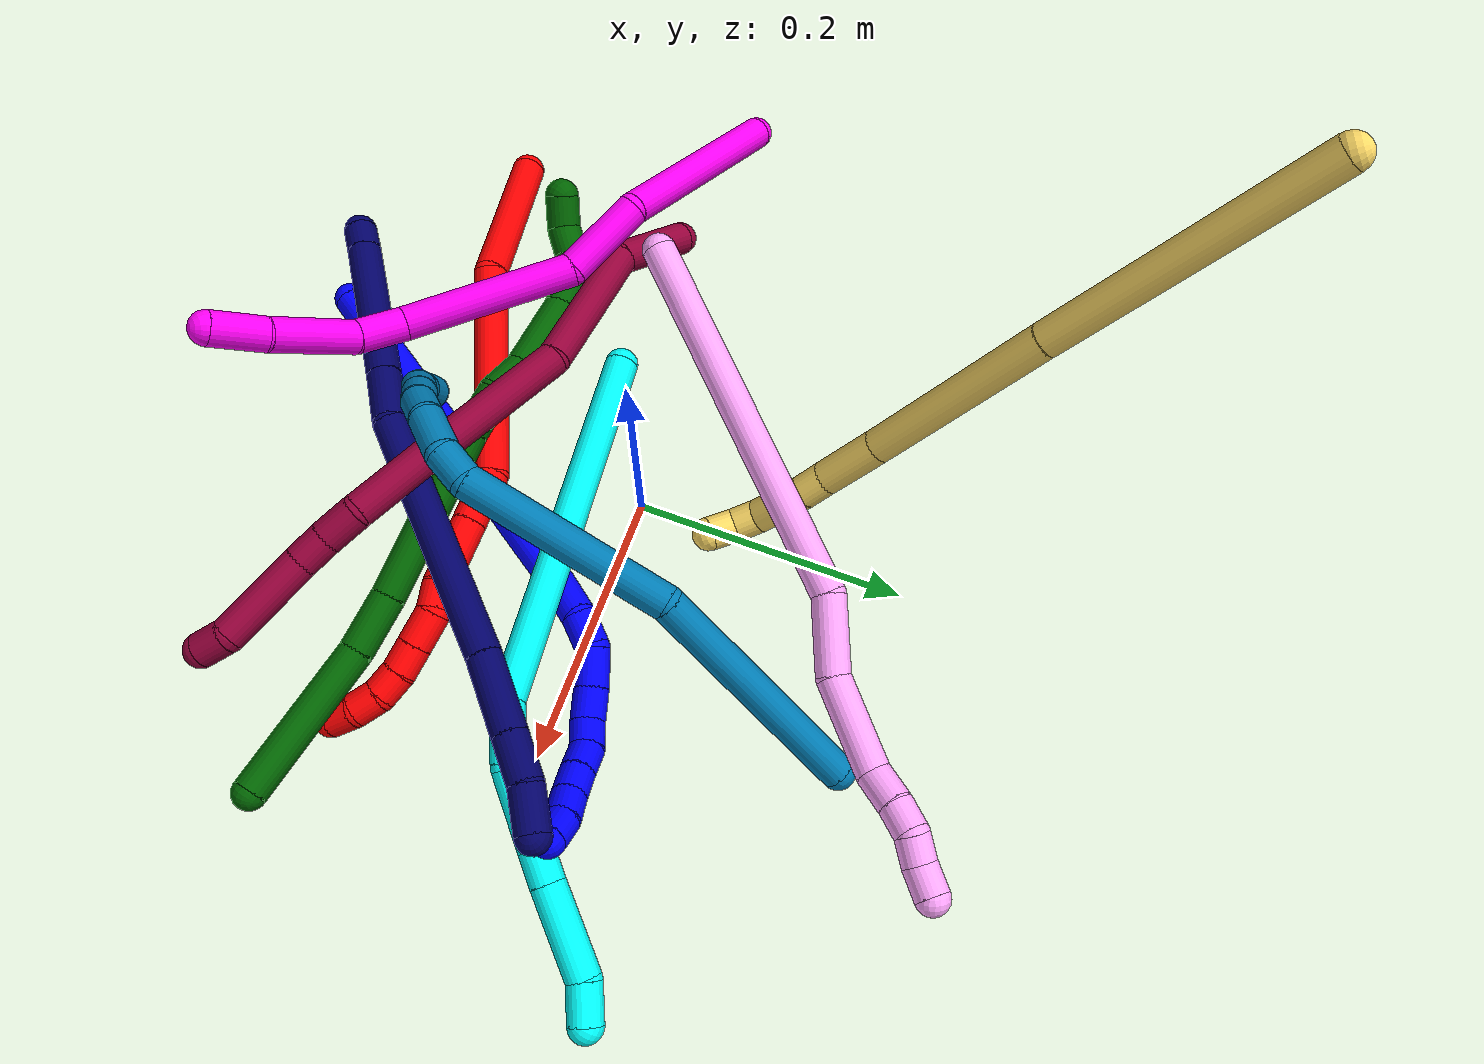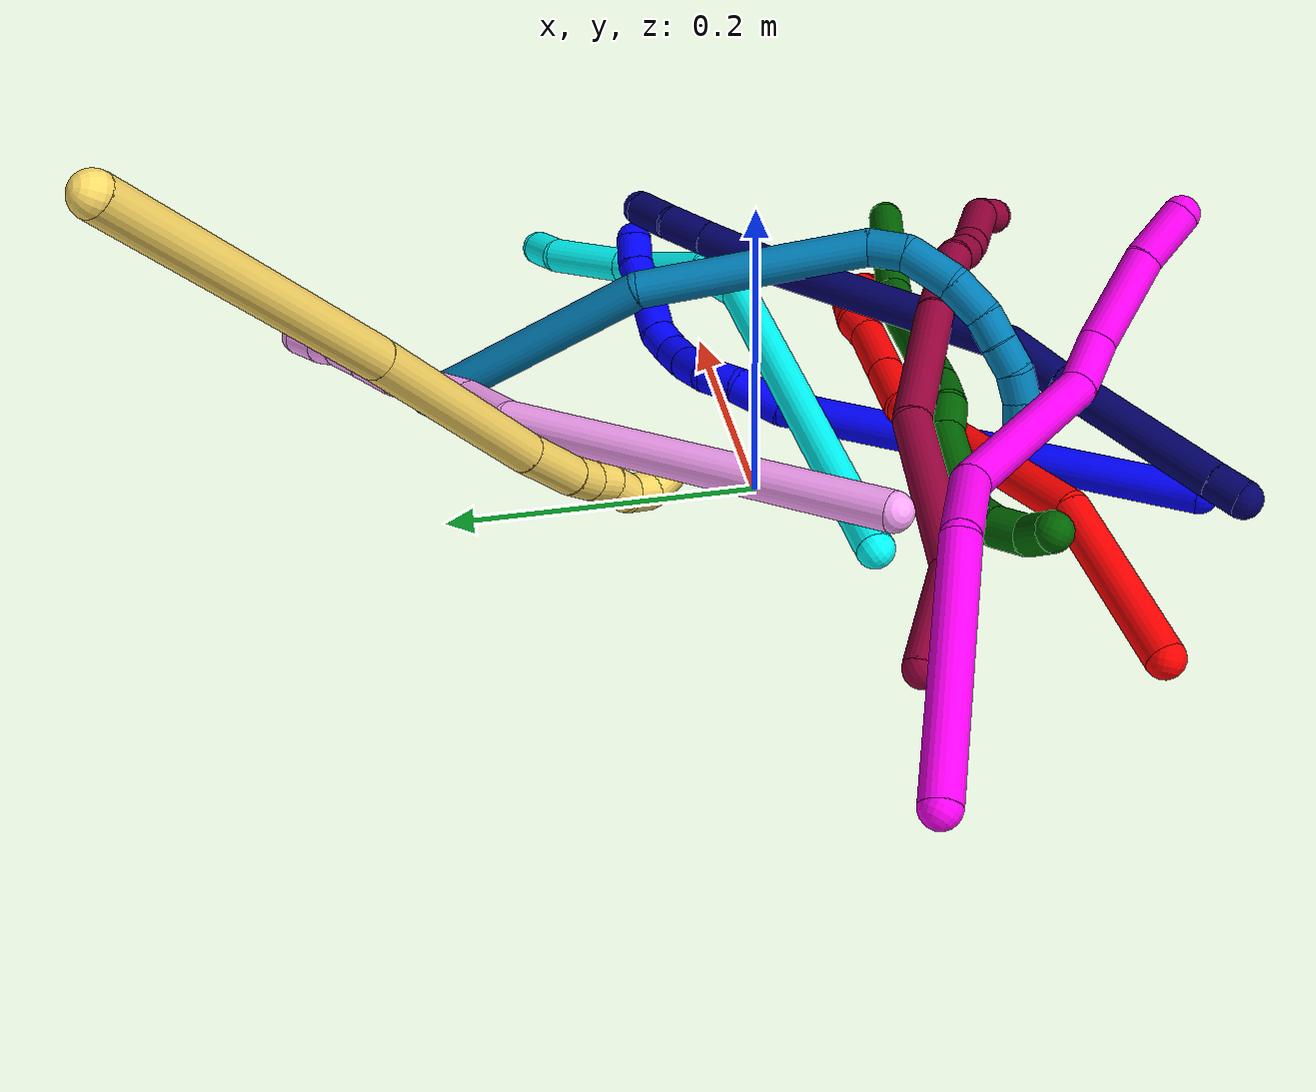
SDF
<sdf version="1.7">
 <world name="default">
  <plugin name="TubeGeneratorPlugin" filename="libtube_generator_plugin.so"/>
  <model name="photoneo_s_sensor">
   <static>1</static>
   <pose>0 0 2 1.57079 1.57079 3.14159</pose>
   <link name="link">
    <inertial><mass>0.1</mass></inertial>
    <sensor name="sensor" type="depth">
     <update_rate>30</update_rate>
     <camera>
      <horizontal_fov>1.22</horizontal_fov>
      <image><width>1920</width><height>1200</height><format>B8G8R8</format></image>
      <clip><near>0.1</near><far>2</far></clip>
      <depth_camera><output>points</output></depth_camera>
     </camera>
     <plugin name="camera_plugin" filename="libgazebo_ros_depth_camera.so">
      <baseline>0.2</baseline>
      <alwaysOn>1</alwaysOn>
      <updateRate>0.0</updateRate>
      <cameraName>camera_ir</cameraName>
      <imageTopicName>/camera/color/image_raw</imageTopicName>
      <cameraInfoTopicName>/camera/color/camera_info</cameraInfoTopicName>
      <depthImageTopicName>/camera/depth/image_raw</depthImageTopicName>
      <depthImageCameraInfoTopicName>/camera/depth/camera_info</depthImageCameraInfoTopicName>
      <pointCloudTopicName>/camera/depth/points</pointCloudTopicName>
      <frameName>fr_optical</frameName>
      <pointCloudCutoff>0.1</pointCloudCutoff>
      <pointCloudCutoffMax>2.0</pointCloudCutoffMax>
      <distortionK1>0</distortionK1>
      <distortionK2>0</distortionK2>
      <distortionK3>0</distortionK3>
      <distortionT1>0</distortionT1>
      <distortionT2>0</distortionT2>
      <CxPrime>0</CxPrime>
      <Cx>0</Cx>
      <Cy>0</Cy>
      <focalLength>0</focalLength>
      <hackBaseline>0</hackBaseline>
     </plugin>
    </sensor>
   </link>
  </model>
  <gravity>0 0 -9.8</gravity>
  <magnetic_field>6e-06 2.3e-05 -4.2e-05</magnetic_field>
  <atmosphere type="adiabatic"/>
  <physics name="default_physics" default="0" type="ode">
   <max_step_size>0.003</max_step_size>
   <real_time_factor>1</real_time_factor>
   <real_time_update_rate>1000</real_time_update_rate>
   <max_contacts>10000</max_contacts>
   <ode>
    <solver>
     <type>quick</type>
     <iters>100</iters>
     <sor>1.3</sor>
     <use_dynamic_moi_rescaling>0</use_dynamic_moi_rescaling>
    </solver>
    <constraints>
     <contact_max_correcting_vel>0</contact_max_correcting_vel>
     <contact_surface_layer>0.001</contact_surface_layer>
     <cfm>0</cfm>
     <erp>0.2</erp>
    </constraints>
   </ode>
  </physics>
  <scene><ambient>0.4 0.4 0.4 1</ambient><background>0.7 0.7 0.7 1</background><shadows>0</shadows></scene>
  <audio><device>default</device></audio>
  <spherical_coordinates>
   <surface_model>EARTH_WGS84</surface_model>
   <latitude_deg>0</latitude_deg>
   <longitude_deg>0</longitude_deg>
   <elevation>0</elevation>
   <heading_deg>0</heading_deg>
  </spherical_coordinates>
  <model name="bin">
   <static>1</static>
   <link name="bottom">
    <collision name="collision-bottom">
     <pose>0 0 -0.01 0 -0 0</pose>
     <geometry><box><size>0.8 0.6 0.02</size></box></geometry>
     <surface>
      <friction><ode><mu>100</mu><mu2>100</mu2></ode></friction>
      <contact><collide_bitmask>65535</collide_bitmask></contact>
     </surface>
    </collision>
   </link>
   <link name="west_wall">
    <collision name="collision-west_wall">
     <pose>-0.41 0 0.1 0 -0 0</pose>
     <geometry><box><size>0.02 0.6 0.2</size></box></geometry>
     <surface>
      <friction><ode><mu>100</mu><mu2>100</mu2></ode></friction>
      <contact><collide_bitmask>65535</collide_bitmask></contact>
     </surface>
    </collision>
   </link>
   <link name="east_wall">
    <collision name="collision-east_wall">
     <pose>0.41 0 0.1 0 -0 0</pose>
     <geometry><box><size>0.02 0.6 0.2</size></box></geometry>
     <surface>
      <friction><ode><mu>100</mu><mu2>100</mu2></ode></friction>
      <contact><collide_bitmask>65535</collide_bitmask></contact>
     </surface>
    </collision>
   </link>
   <link name="south_wall">
    <collision name="collision-south_wall">
     <pose>0 -0.31 0.1 0 -0 0</pose>
     <geometry><box><size>0.8 0.02 0.2</size></box></geometry>
     <surface>
      <friction><ode><mu>100</mu><mu2>100</mu2></ode></friction>
      <contact><collide_bitmask>65535</collide_bitmask></contact>
     </surface>
    </collision>
   </link>
   <link name="north_wall">
    <collision name="collision-north_wall">
     <pose>0 0.31 0.1 0 -0 0</pose>
     <geometry><box><size>0.8 0.02 0.2</size></box></geometry>
     <surface>
      <friction><ode><mu>100</mu><mu2>100</mu2></ode></friction>
      <contact><collide_bitmask>65535</collide_bitmask></contact>
     </surface>
    </collision>
   </link>
  </model>
  <model name="1">
   <static>0</static>
   <link name="1">
    <collision name="collision-cylinder-e_1_1_4">
     <pose>0.094757 0.101555 0.031999 -1.26556 0.727224 -0.5443</pose>
     <geometry><cylinder><radius>0.0125</radius><length>0.285071</length></cylinder></geometry>
     <surface>
      <friction><ode><mu>1.16</mu><mu2>1.16</mu2><slip1>0</slip1><slip2>0</slip2></ode></friction>
      <contact><ode><kp>1e+06</kp><kd>1</kd><max_vel>0</max_vel><min_depth>0.001</min_depth></ode></contact>
     </surface>
    </collision>
    <visual name="visual-cylinder-e_1_1_4">
     <pose>0.094757 0.101555 0.031999 -1.26556 0.727224 -0.5443</pose>
     <geometry><cylinder><radius>0.0125</radius><length>0.285071</length></cylinder></geometry>
     <material><ambient>0 0 1 1</ambient></material>
    </visual>
    <collision name="collision-cylinder-e_2_4_5">
     <pose>0.200148 0.217335 0.063665 -1.59417 0.641839 -0.655963</pose>
     <geometry><cylinder><radius>0.0125</radius><length>0.035526</length></cylinder></geometry>
     <surface>
      <friction><ode><mu>1.16</mu><mu2>1.16</mu2><slip1>0</slip1><slip2>0</slip2></ode></friction>
      <contact><ode><kp>1e+06</kp><kd>1</kd><max_vel>0</max_vel><min_depth>0.001</min_depth></ode></contact>
     </surface>
    </collision>
    <visual name="visual-cylinder-e_2_4_5">
     <pose>0.200148 0.217335 0.063665 -1.59417 0.641839 -0.655963</pose>
     <geometry><cylinder><radius>0.0125</radius><length>0.035526</length></cylinder></geometry>
     <material><ambient>0 0 1 1</ambient></material>
    </visual>
    <collision name="collision-cylinder-e_3_5_6">
     <pose>0.217127 0.24212 0.066509 -1.27857 0.522029 -0.392053</pose>
     <geometry><cylinder><radius>0.0125</radius><length>0.025446</length></cylinder></geometry>
     <surface>
      <friction><ode><mu>1.16</mu><mu2>1.16</mu2><slip1>0</slip1><slip2>0</slip2></ode></friction>
      <contact><ode><kp>1e+06</kp><kd>1</kd><max_vel>0</max_vel><min_depth>0.001</min_depth></ode></contact>
     </surface>
    </collision>
    <visual name="visual-cylinder-e_3_5_6">
     <pose>0.217127 0.24212 0.066509 -1.27857 0.522029 -0.392053</pose>
     <geometry><cylinder><radius>0.0125</radius><length>0.025446</length></cylinder></geometry>
     <material><ambient>0 0 1 1</ambient></material>
    </visual>
    <collision name="collision-cylinder-e_4_6_7">
     <pose>0.224424 0.265693 0.075253 -1.1666 0.067213 -0.044363</pose>
     <geometry><cylinder><radius>0.0125</radius><length>0.02837</length></cylinder></geometry>
     <surface>
      <friction><ode><mu>1.16</mu><mu2>1.16</mu2><slip1>0</slip1><slip2>0</slip2></ode></friction>
      <contact><ode><kp>1e+06</kp><kd>1</kd><max_vel>0</max_vel><min_depth>0.001</min_depth></ode></contact>
     </surface>
    </collision>
    <visual name="visual-cylinder-e_4_6_7">
     <pose>0.224424 0.265693 0.075253 -1.1666 0.067213 -0.044363</pose>
     <geometry><cylinder><radius>0.0125</radius><length>0.02837</length></cylinder></geometry>
     <material><ambient>0 0 1 1</ambient></material>
    </visual>
    <collision name="collision-cylinder-e_5_7_8">
     <pose>0.225427 0.290047 0.084431 -1.26249 0.004249 -0.003106</pose>
     <geometry><cylinder><radius>0.0125</radius><length>0.023807</length></cylinder></geometry>
     <surface>
      <friction><ode><mu>1.16</mu><mu2>1.16</mu2><slip1>0</slip1><slip2>0</slip2></ode></friction>
      <contact><ode><kp>1e+06</kp><kd>1</kd><max_vel>0</max_vel><min_depth>0.001</min_depth></ode></contact>
     </surface>
    </collision>
    <visual name="visual-cylinder-e_5_7_8">
     <pose>0.225427 0.290047 0.084431 -1.26249 0.004249 -0.003106</pose>
     <geometry><cylinder><radius>0.0125</radius><length>0.023807</length></cylinder></geometry>
     <material><ambient>0 0 1 1</ambient></material>
    </visual>
    <collision name="collision-cylinder-e_6_8_9">
     <pose>0.226951 0.311512 0.087967 -1.57832 0.14455 -0.145638</pose>
     <geometry><cylinder><radius>0.0125</radius><length>0.020458</length></cylinder></geometry>
     <surface>
      <friction><ode><mu>1.16</mu><mu2>1.16</mu2><slip1>0</slip1><slip2>0</slip2></ode></friction>
      <contact><ode><kp>1e+06</kp><kd>1</kd><max_vel>0</max_vel><min_depth>0.001</min_depth></ode></contact>
     </surface>
    </collision>
    <visual name="visual-cylinder-e_6_8_9">
     <pose>0.226951 0.311512 0.087967 -1.57832 0.14455 -0.145638</pose>
     <geometry><cylinder><radius>0.0125</radius><length>0.020458</length></cylinder></geometry>
     <material><ambient>0 0 1 1</ambient></material>
    </visual>
    <collision name="collision-cylinder-e_7_9_10">
     <pose>0.227167 0.331533 0.0852 -1.83621 -0.121956 0.159392</pose>
     <geometry><cylinder><radius>0.0125</radius><length>0.02067</length></cylinder></geometry>
     <surface>
      <friction><ode><mu>1.16</mu><mu2>1.16</mu2><slip1>0</slip1><slip2>0</slip2></ode></friction>
      <contact><ode><kp>1e+06</kp><kd>1</kd><max_vel>0</max_vel><min_depth>0.001</min_depth></ode></contact>
     </surface>
    </collision>
    <visual name="visual-cylinder-e_7_9_10">
     <pose>0.227167 0.331533 0.0852 -1.83621 -0.121956 0.159392</pose>
     <geometry><cylinder><radius>0.0125</radius><length>0.02067</length></cylinder></geometry>
     <material><ambient>0 0 1 1</ambient></material>
    </visual>
    <collision name="collision-cylinder-e_8_10_11">
     <pose>0.224991 0.351176 0.080162 -1.80718 -0.091384 0.115961</pose>
     <geometry><cylinder><radius>0.0125</radius><length>0.02013</length></cylinder></geometry>
     <surface>
      <friction><ode><mu>1.16</mu><mu2>1.16</mu2><slip1>0</slip1><slip2>0</slip2></ode></friction>
      <contact><ode><kp>1e+06</kp><kd>1</kd><max_vel>0</max_vel><min_depth>0.001</min_depth></ode></contact>
     </surface>
    </collision>
    <visual name="visual-cylinder-e_8_10_11">
     <pose>0.224991 0.351176 0.080162 -1.80718 -0.091384 0.115961</pose>
     <geometry><cylinder><radius>0.0125</radius><length>0.02013</length></cylinder></geometry>
     <material><ambient>0 0 1 1</ambient></material>
    </visual>
    <collision name="collision-cylinder-e_9_11_12">
     <pose>0.223972 0.370537 0.074639 -1.8897 -0.009973 0.013795</pose>
     <geometry><cylinder><radius>0.0125</radius><length>0.020253</length></cylinder></geometry>
     <surface>
      <friction><ode><mu>1.16</mu><mu2>1.16</mu2><slip1>0</slip1><slip2>0</slip2></ode></friction>
      <contact><ode><kp>1e+06</kp><kd>1</kd><max_vel>0</max_vel><min_depth>0.001</min_depth></ode></contact>
     </surface>
    </collision>
    <visual name="visual-cylinder-e_9_11_12">
     <pose>0.223972 0.370537 0.074639 -1.8897 -0.009973 0.013795</pose>
     <geometry><cylinder><radius>0.0125</radius><length>0.020253</length></cylinder></geometry>
     <material><ambient>0 0 1 1</ambient></material>
    </visual>
    <collision name="collision-cylinder-e_10_12_2">
     <pose>0.22141 0.389041 0.067265 -2.01215 -0.245281 0.38431</pose>
     <geometry><cylinder><radius>0.0125</radius><length>0.020269</length></cylinder></geometry>
     <surface>
      <friction><ode><mu>1.16</mu><mu2>1.16</mu2><slip1>0</slip1><slip2>0</slip2></ode></friction>
      <contact><ode><kp>1e+06</kp><kd>1</kd><max_vel>0</max_vel><min_depth>0.001</min_depth></ode></contact>
     </surface>
    </collision>
    <visual name="visual-cylinder-e_10_12_2">
     <pose>0.22141 0.389041 0.067265 -2.01215 -0.245281 0.38431</pose>
     <geometry><cylinder><radius>0.0125</radius><length>0.020269</length></cylinder></geometry>
     <material><ambient>0 0 1 1</ambient></material>
    </visual>
    <collision name="collision-sphere-2">
     <pose>0.218949 0.39793 0.063066 0 -0 0</pose>
     <geometry><sphere><radius>0.0125</radius></sphere></geometry>
     <surface>
      <friction><ode><mu>1.16</mu><mu2>1.16</mu2><slip1>0</slip1><slip2>0</slip2></ode></friction>
      <contact><ode><kp>1e+06</kp><kd>1</kd><max_vel>0</max_vel><min_depth>0.001</min_depth></ode></contact>
     </surface>
    </collision>
    <visual name="visual-sphere-2">
     <pose>0.218949 0.39793 0.063066 0 -0 0</pose>
     <geometry><sphere><radius>0.0125</radius></sphere></geometry>
     <material><ambient>0 0 1 1</ambient></material>
    </visual>
    <collision name="collision-sphere-12">
     <pose>0.223871 0.380152 0.071465 0 -0 0</pose>
     <geometry><sphere><radius>0.0125</radius></sphere></geometry>
     <surface>
      <friction><ode><mu>1.16</mu><mu2>1.16</mu2><slip1>0</slip1><slip2>0</slip2></ode></friction>
      <contact><ode><kp>1e+06</kp><kd>1</kd><max_vel>0</max_vel><min_depth>0.001</min_depth></ode></contact>
     </surface>
    </collision>
    <visual name="visual-sphere-12">
     <pose>0.223871 0.380152 0.071465 0 -0 0</pose>
     <geometry><sphere><radius>0.0125</radius></sphere></geometry>
     <material><ambient>0 0 1 1</ambient></material>
    </visual>
    <collision name="collision-sphere-11">
     <pose>0.224073 0.360921 0.077814 0 -0 0</pose>
     <geometry><sphere><radius>0.0125</radius></sphere></geometry>
     <surface>
      <friction><ode><mu>1.16</mu><mu2>1.16</mu2><slip1>0</slip1><slip2>0</slip2></ode></friction>
      <contact><ode><kp>1e+06</kp><kd>1</kd><max_vel>0</max_vel><min_depth>0.001</min_depth></ode></contact>
     </surface>
    </collision>
    <visual name="visual-sphere-11">
     <pose>0.224073 0.360921 0.077814 0 -0 0</pose>
     <geometry><sphere><radius>0.0125</radius></sphere></geometry>
     <material><ambient>0 0 1 1</ambient></material>
    </visual>
    <collision name="collision-sphere-10">
     <pose>0.22591 0.341432 0.082509 0 -0 0</pose>
     <geometry><sphere><radius>0.0125</radius></sphere></geometry>
     <surface>
      <friction><ode><mu>1.16</mu><mu2>1.16</mu2><slip1>0</slip1><slip2>0</slip2></ode></friction>
      <contact><ode><kp>1e+06</kp><kd>1</kd><max_vel>0</max_vel><min_depth>0.001</min_depth></ode></contact>
     </surface>
    </collision>
    <visual name="visual-sphere-10">
     <pose>0.22591 0.341432 0.082509 0 -0 0</pose>
     <geometry><sphere><radius>0.0125</radius></sphere></geometry>
     <material><ambient>0 0 1 1</ambient></material>
    </visual>
    <collision name="collision-sphere-9">
     <pose>0.228424 0.321633 0.087891 0 -0 0</pose>
     <geometry><sphere><radius>0.0125</radius></sphere></geometry>
     <surface>
      <friction><ode><mu>1.16</mu><mu2>1.16</mu2><slip1>0</slip1><slip2>0</slip2></ode></friction>
      <contact><ode><kp>1e+06</kp><kd>1</kd><max_vel>0</max_vel><min_depth>0.001</min_depth></ode></contact>
     </surface>
    </collision>
    <visual name="visual-sphere-9">
     <pose>0.228424 0.321633 0.087891 0 -0 0</pose>
     <geometry><sphere><radius>0.0125</radius></sphere></geometry>
     <material><ambient>0 0 1 1</ambient></material>
    </visual>
    <collision name="collision-sphere-4">
     <pose>0.189514 0.20311 0.063997 0 -0 0</pose>
     <geometry><sphere><radius>0.0125</radius></sphere></geometry>
     <surface>
      <friction><ode><mu>1.16</mu><mu2>1.16</mu2><slip1>0</slip1><slip2>0</slip2></ode></friction>
      <contact><ode><kp>1e+06</kp><kd>1</kd><max_vel>0</max_vel><min_depth>0.001</min_depth></ode></contact>
     </surface>
    </collision>
    <visual name="visual-sphere-4">
     <pose>0.189514 0.20311 0.063997 0 -0 0</pose>
     <geometry><sphere><radius>0.0125</radius></sphere></geometry>
     <material><ambient>0 0 1 1</ambient></material>
    </visual>
    <collision name="collision-sphere-1">
     <geometry><sphere><radius>0.0125</radius></sphere></geometry>
     <surface>
      <friction><ode><mu>1.16</mu><mu2>1.16</mu2><slip1>0</slip1><slip2>0</slip2></ode></friction>
      <contact><ode><kp>1e+06</kp><kd>1</kd><max_vel>0</max_vel><min_depth>0.001</min_depth></ode></contact>
     </surface>
    </collision>
    <visual name="visual-sphere-1">
     <geometry><sphere><radius>0.0125</radius></sphere></geometry>
     <material><ambient>0 0 1 1</ambient></material>
    </visual>
    <collision name="collision-sphere-8">
     <pose>0.225477 0.30139 0.088043 0 -0 0</pose>
     <geometry><sphere><radius>0.0125</radius></sphere></geometry>
     <surface>
      <friction><ode><mu>1.16</mu><mu2>1.16</mu2><slip1>0</slip1><slip2>0</slip2></ode></friction>
      <contact><ode><kp>1e+06</kp><kd>1</kd><max_vel>0</max_vel><min_depth>0.001</min_depth></ode></contact>
     </surface>
    </collision>
    <visual name="visual-sphere-8">
     <pose>0.225477 0.30139 0.088043 0 -0 0</pose>
     <geometry><sphere><radius>0.0125</radius></sphere></geometry>
     <material><ambient>0 0 1 1</ambient></material>
    </visual>
    <collision name="collision-sphere-5">
     <pose>0.210783 0.231559 0.063332 0 -0 0</pose>
     <geometry><sphere><radius>0.0125</radius></sphere></geometry>
     <surface>
      <friction><ode><mu>1.16</mu><mu2>1.16</mu2><slip1>0</slip1><slip2>0</slip2></ode></friction>
      <contact><ode><kp>1e+06</kp><kd>1</kd><max_vel>0</max_vel><min_depth>0.001</min_depth></ode></contact>
     </surface>
    </collision>
    <visual name="visual-sphere-5">
     <pose>0.210783 0.231559 0.063332 0 -0 0</pose>
     <geometry><sphere><radius>0.0125</radius></sphere></geometry>
     <material><ambient>0 0 1 1</ambient></material>
    </visual>
    <collision name="collision-sphere-6">
     <pose>0.223471 0.25268 0.069687 0 -0 0</pose>
     <geometry><sphere><radius>0.0125</radius></sphere></geometry>
     <surface>
      <friction><ode><mu>1.16</mu><mu2>1.16</mu2><slip1>0</slip1><slip2>0</slip2></ode></friction>
      <contact><ode><kp>1e+06</kp><kd>1</kd><max_vel>0</max_vel><min_depth>0.001</min_depth></ode></contact>
     </surface>
    </collision>
    <visual name="visual-sphere-6">
     <pose>0.223471 0.25268 0.069687 0 -0 0</pose>
     <geometry><sphere><radius>0.0125</radius></sphere></geometry>
     <material><ambient>0 0 1 1</ambient></material>
    </visual>
    <collision name="collision-sphere-7">
     <pose>0.225376 0.278705 0.080819 0 -0 0</pose>
     <geometry><sphere><radius>0.0125</radius></sphere></geometry>
     <surface>
      <friction><ode><mu>1.16</mu><mu2>1.16</mu2><slip1>0</slip1><slip2>0</slip2></ode></friction>
      <contact><ode><kp>1e+06</kp><kd>1</kd><max_vel>0</max_vel><min_depth>0.001</min_depth></ode></contact>
     </surface>
    </collision>
    <visual name="visual-sphere-7">
     <pose>0.225376 0.278705 0.080819 0 -0 0</pose>
     <geometry><sphere><radius>0.0125</radius></sphere></geometry>
     <material><ambient>0 0 1 1</ambient></material>
    </visual>
    <inertial>
     <pose>0.148546 0.185921 0.050541 0 -0 0</pose>
     <mass>0.5</mass>
     <inertia>
      <ixx>0.000522</ixx>
      <ixy>0</ixy>
      <ixz>0</ixz>
      <iyy>0.000417</iyy>
      <iyz>0</iyz>
      <izz>-0.002691</izz>
     </inertia>
    </inertial>
   </link>
   <pose>-0.078273 -0.272883 0.011501 2.9055 -0.077396 1.82902</pose>
  </model>
  <model name="2">
   <static>0</static>
   <link name="2">
    <collision name="collision-cylinder-e_1_1_4">
     <pose>0.045639 0.012044 0.035538 -0.326761 0.882673 -0.155441</pose>
     <geometry><cylinder><radius>0.0125</radius><length>0.118168</length></cylinder></geometry>
     <surface>
      <friction><ode><mu>1.16</mu><mu2>1.16</mu2><slip1>0</slip1><slip2>0</slip2></ode></friction>
      <contact><ode><kp>1e+06</kp><kd>1</kd><max_vel>0</max_vel><min_depth>0.001</min_depth></ode></contact>
     </surface>
    </collision>
    <visual name="visual-cylinder-e_1_1_4">
     <pose>0.045639 0.012044 0.035538 -0.326761 0.882673 -0.155441</pose>
     <geometry><cylinder><radius>0.0125</radius><length>0.118168</length></cylinder></geometry>
     <material><ambient>1 0 0 1</ambient></material>
    </visual>
    <collision name="collision-cylinder-e_2_4_5">
     <pose>0.166402 0.046902 0.091939 -0.83001 1.1804 -0.573969</pose>
     <geometry><cylinder><radius>0.0125</radius><length>0.162474</length></cylinder></geometry>
     <surface>
      <friction><ode><mu>1.16</mu><mu2>1.16</mu2><slip1>0</slip1><slip2>0</slip2></ode></friction>
      <contact><ode><kp>1e+06</kp><kd>1</kd><max_vel>0</max_vel><min_depth>0.001</min_depth></ode></contact>
     </surface>
    </collision>
    <visual name="visual-cylinder-e_2_4_5">
     <pose>0.166402 0.046902 0.091939 -0.83001 1.1804 -0.573969</pose>
     <geometry><cylinder><radius>0.0125</radius><length>0.162474</length></cylinder></geometry>
     <material><ambient>1 0 0 1</ambient></material>
    </visual>
    <collision name="collision-cylinder-e_3_5_6">
     <pose>0.259366 0.068783 0.123188 0.089501 1.04187 0.051379</pose>
     <geometry><cylinder><radius>0.0125</radius><length>0.041325</length></cylinder></geometry>
     <surface>
      <friction><ode><mu>1.16</mu><mu2>1.16</mu2><slip1>0</slip1><slip2>0</slip2></ode></friction>
      <contact><ode><kp>1e+06</kp><kd>1</kd><max_vel>0</max_vel><min_depth>0.001</min_depth></ode></contact>
     </surface>
    </collision>
    <visual name="visual-cylinder-e_3_5_6">
     <pose>0.259366 0.068783 0.123188 0.089501 1.04187 0.051379</pose>
     <geometry><cylinder><radius>0.0125</radius><length>0.041325</length></cylinder></geometry>
     <material><ambient>1 0 0 1</ambient></material>
    </visual>
    <collision name="collision-cylinder-e_4_6_7">
     <pose>0.298591 0.066723 0.145993 0.090544 1.04284 0.052036</pose>
     <geometry><cylinder><radius>0.0125</radius><length>0.049515</length></cylinder></geometry>
     <surface>
      <friction><ode><mu>1.16</mu><mu2>1.16</mu2><slip1>0</slip1><slip2>0</slip2></ode></friction>
      <contact><ode><kp>1e+06</kp><kd>1</kd><max_vel>0</max_vel><min_depth>0.001</min_depth></ode></contact>
     </surface>
    </collision>
    <visual name="visual-cylinder-e_4_6_7">
     <pose>0.298591 0.066723 0.145993 0.090544 1.04284 0.052036</pose>
     <geometry><cylinder><radius>0.0125</radius><length>0.049515</length></cylinder></geometry>
     <material><ambient>1 0 0 1</ambient></material>
    </visual>
    <collision name="collision-cylinder-e_5_7_8">
     <pose>0.329169 0.067107 0.162792 -0.332367 1.1041 -0.205888</pose>
     <geometry><cylinder><radius>0.0125</radius><length>0.020585</length></cylinder></geometry>
     <surface>
      <friction><ode><mu>1.16</mu><mu2>1.16</mu2><slip1>0</slip1><slip2>0</slip2></ode></friction>
      <contact><ode><kp>1e+06</kp><kd>1</kd><max_vel>0</max_vel><min_depth>0.001</min_depth></ode></contact>
     </surface>
    </collision>
    <visual name="visual-cylinder-e_5_7_8">
     <pose>0.329169 0.067107 0.162792 -0.332367 1.1041 -0.205888</pose>
     <geometry><cylinder><radius>0.0125</radius><length>0.020585</length></cylinder></geometry>
     <material><ambient>1 0 0 1</ambient></material>
    </visual>
    <collision name="collision-cylinder-e_6_8_9">
     <pose>0.35004 0.064746 0.17139 0.742254 1.11488 0.476001</pose>
     <geometry><cylinder><radius>0.0125</radius><length>0.026016</length></cylinder></geometry>
     <surface>
      <friction><ode><mu>1.16</mu><mu2>1.16</mu2><slip1>0</slip1><slip2>0</slip2></ode></friction>
      <contact><ode><kp>1e+06</kp><kd>1</kd><max_vel>0</max_vel><min_depth>0.001</min_depth></ode></contact>
     </surface>
    </collision>
    <visual name="visual-cylinder-e_6_8_9">
     <pose>0.35004 0.064746 0.17139 0.742254 1.11488 0.476001</pose>
     <geometry><cylinder><radius>0.0125</radius><length>0.026016</length></cylinder></geometry>
     <material><ambient>1 0 0 1</ambient></material>
    </visual>
    <collision name="collision-cylinder-e_7_9_10">
     <pose>0.371309 0.057676 0.179066 0.746841 1.11437 0.47885</pose>
     <geometry><cylinder><radius>0.0125</radius><length>0.021366</length></cylinder></geometry>
     <surface>
      <friction><ode><mu>1.16</mu><mu2>1.16</mu2><slip1>0</slip1><slip2>0</slip2></ode></friction>
      <contact><ode><kp>1e+06</kp><kd>1</kd><max_vel>0</max_vel><min_depth>0.001</min_depth></ode></contact>
     </surface>
    </collision>
    <visual name="visual-cylinder-e_7_9_10">
     <pose>0.371309 0.057676 0.179066 0.746841 1.11437 0.47885</pose>
     <geometry><cylinder><radius>0.0125</radius><length>0.021366</length></cylinder></geometry>
     <material><ambient>1 0 0 1</ambient></material>
    </visual>
    <collision name="collision-cylinder-e_8_10_11">
     <pose>0.389068 0.049834 0.186375 0.878009 0.934574 0.465266</pose>
     <geometry><cylinder><radius>0.0125</radius><length>0.020314</length></cylinder></geometry>
     <surface>
      <friction><ode><mu>1.16</mu><mu2>1.16</mu2><slip1>0</slip1><slip2>0</slip2></ode></friction>
      <contact><ode><kp>1e+06</kp><kd>1</kd><max_vel>0</max_vel><min_depth>0.001</min_depth></ode></contact>
     </surface>
    </collision>
    <visual name="visual-cylinder-e_8_10_11">
     <pose>0.389068 0.049834 0.186375 0.878009 0.934574 0.465266</pose>
     <geometry><cylinder><radius>0.0125</radius><length>0.020314</length></cylinder></geometry>
     <material><ambient>1 0 0 1</ambient></material>
    </visual>
    <collision name="collision-cylinder-e_9_11_12">
     <pose>0.40321 0.037993 0.193858 1.10389 0.637624 0.401044</pose>
     <geometry><cylinder><radius>0.0125</radius><length>0.020063</length></cylinder></geometry>
     <surface>
      <friction><ode><mu>1.16</mu><mu2>1.16</mu2><slip1>0</slip1><slip2>0</slip2></ode></friction>
      <contact><ode><kp>1e+06</kp><kd>1</kd><max_vel>0</max_vel><min_depth>0.001</min_depth></ode></contact>
     </surface>
    </collision>
    <visual name="visual-cylinder-e_9_11_12">
     <pose>0.40321 0.037993 0.193858 1.10389 0.637624 0.401044</pose>
     <geometry><cylinder><radius>0.0125</radius><length>0.020063</length></cylinder></geometry>
     <material><ambient>1 0 0 1</ambient></material>
    </visual>
    <collision name="collision-cylinder-e_10_12_2">
     <pose>0.413736 0.021863 0.198594 1.44745 0.468472 0.415632</pose>
     <geometry><cylinder><radius>0.0125</radius><length>0.020174</length></cylinder></geometry>
     <surface>
      <friction><ode><mu>1.16</mu><mu2>1.16</mu2><slip1>0</slip1><slip2>0</slip2></ode></friction>
      <contact><ode><kp>1e+06</kp><kd>1</kd><max_vel>0</max_vel><min_depth>0.001</min_depth></ode></contact>
     </surface>
    </collision>
    <visual name="visual-cylinder-e_10_12_2">
     <pose>0.413736 0.021863 0.198594 1.44745 0.468472 0.415632</pose>
     <geometry><cylinder><radius>0.0125</radius><length>0.020174</length></cylinder></geometry>
     <material><ambient>1 0 0 1</ambient></material>
    </visual>
    <collision name="collision-sphere-2">
     <pose>0.418291 0.012931 0.199701 0 -0 0</pose>
     <geometry><sphere><radius>0.0125</radius></sphere></geometry>
     <surface>
      <friction><ode><mu>1.16</mu><mu2>1.16</mu2><slip1>0</slip1><slip2>0</slip2></ode></friction>
      <contact><ode><kp>1e+06</kp><kd>1</kd><max_vel>0</max_vel><min_depth>0.001</min_depth></ode></contact>
     </surface>
    </collision>
    <visual name="visual-sphere-2">
     <pose>0.418291 0.012931 0.199701 0 -0 0</pose>
     <geometry><sphere><radius>0.0125</radius></sphere></geometry>
     <material><ambient>1 0 0 1</ambient></material>
    </visual>
    <collision name="collision-sphere-12">
     <pose>0.409182 0.030795 0.197486 0 -0 0</pose>
     <geometry><sphere><radius>0.0125</radius></sphere></geometry>
     <surface>
      <friction><ode><mu>1.16</mu><mu2>1.16</mu2><slip1>0</slip1><slip2>0</slip2></ode></friction>
      <contact><ode><kp>1e+06</kp><kd>1</kd><max_vel>0</max_vel><min_depth>0.001</min_depth></ode></contact>
     </surface>
    </collision>
    <visual name="visual-sphere-12">
     <pose>0.409182 0.030795 0.197486 0 -0 0</pose>
     <geometry><sphere><radius>0.0125</radius></sphere></geometry>
     <material><ambient>1 0 0 1</ambient></material>
    </visual>
    <collision name="collision-sphere-11">
     <pose>0.397238 0.04519 0.19023 0 -0 0</pose>
     <geometry><sphere><radius>0.0125</radius></sphere></geometry>
     <surface>
      <friction><ode><mu>1.16</mu><mu2>1.16</mu2><slip1>0</slip1><slip2>0</slip2></ode></friction>
      <contact><ode><kp>1e+06</kp><kd>1</kd><max_vel>0</max_vel><min_depth>0.001</min_depth></ode></contact>
     </surface>
    </collision>
    <visual name="visual-sphere-11">
     <pose>0.397238 0.04519 0.19023 0 -0 0</pose>
     <geometry><sphere><radius>0.0125</radius></sphere></geometry>
     <material><ambient>1 0 0 1</ambient></material>
    </visual>
    <collision name="collision-sphere-10">
     <pose>0.380899 0.054478 0.182521 0 -0 0</pose>
     <geometry><sphere><radius>0.0125</radius></sphere></geometry>
     <surface>
      <friction><ode><mu>1.16</mu><mu2>1.16</mu2><slip1>0</slip1><slip2>0</slip2></ode></friction>
      <contact><ode><kp>1e+06</kp><kd>1</kd><max_vel>0</max_vel><min_depth>0.001</min_depth></ode></contact>
     </surface>
    </collision>
    <visual name="visual-sphere-10">
     <pose>0.380899 0.054478 0.182521 0 -0 0</pose>
     <geometry><sphere><radius>0.0125</radius></sphere></geometry>
     <material><ambient>1 0 0 1</ambient></material>
    </visual>
    <collision name="collision-sphere-9">
     <pose>0.361719 0.060875 0.17561 0 -0 0</pose>
     <geometry><sphere><radius>0.0125</radius></sphere></geometry>
     <surface>
      <friction><ode><mu>1.16</mu><mu2>1.16</mu2><slip1>0</slip1><slip2>0</slip2></ode></friction>
      <contact><ode><kp>1e+06</kp><kd>1</kd><max_vel>0</max_vel><min_depth>0.001</min_depth></ode></contact>
     </surface>
    </collision>
    <visual name="visual-sphere-9">
     <pose>0.361719 0.060875 0.17561 0 -0 0</pose>
     <geometry><sphere><radius>0.0125</radius></sphere></geometry>
     <material><ambient>1 0 0 1</ambient></material>
    </visual>
    <collision name="collision-sphere-4">
     <pose>0.091277 0.024088 0.071076 0 -0 0</pose>
     <geometry><sphere><radius>0.0125</radius></sphere></geometry>
     <surface>
      <friction><ode><mu>1.16</mu><mu2>1.16</mu2><slip1>0</slip1><slip2>0</slip2></ode></friction>
      <contact><ode><kp>1e+06</kp><kd>1</kd><max_vel>0</max_vel><min_depth>0.001</min_depth></ode></contact>
     </surface>
    </collision>
    <visual name="visual-sphere-4">
     <pose>0.091277 0.024088 0.071076 0 -0 0</pose>
     <geometry><sphere><radius>0.0125</radius></sphere></geometry>
     <material><ambient>1 0 0 1</ambient></material>
    </visual>
    <collision name="collision-sphere-1">
     <geometry><sphere><radius>0.0125</radius></sphere></geometry>
     <surface>
      <friction><ode><mu>1.16</mu><mu2>1.16</mu2><slip1>0</slip1><slip2>0</slip2></ode></friction>
      <contact><ode><kp>1e+06</kp><kd>1</kd><max_vel>0</max_vel><min_depth>0.001</min_depth></ode></contact>
     </surface>
    </collision>
    <visual name="visual-sphere-1">
     <geometry><sphere><radius>0.0125</radius></sphere></geometry>
     <material><ambient>1 0 0 1</ambient></material>
    </visual>
    <collision name="collision-sphere-8">
     <pose>0.338361 0.068618 0.167169 0 -0 0</pose>
     <geometry><sphere><radius>0.0125</radius></sphere></geometry>
     <surface>
      <friction><ode><mu>1.16</mu><mu2>1.16</mu2><slip1>0</slip1><slip2>0</slip2></ode></friction>
      <contact><ode><kp>1e+06</kp><kd>1</kd><max_vel>0</max_vel><min_depth>0.001</min_depth></ode></contact>
     </surface>
    </collision>
    <visual name="visual-sphere-8">
     <pose>0.338361 0.068618 0.167169 0 -0 0</pose>
     <geometry><sphere><radius>0.0125</radius></sphere></geometry>
     <material><ambient>1 0 0 1</ambient></material>
    </visual>
    <collision name="collision-sphere-5">
     <pose>0.241527 0.069715 0.112803 0 -0 0</pose>
     <geometry><sphere><radius>0.0125</radius></sphere></geometry>
     <surface>
      <friction><ode><mu>1.16</mu><mu2>1.16</mu2><slip1>0</slip1><slip2>0</slip2></ode></friction>
      <contact><ode><kp>1e+06</kp><kd>1</kd><max_vel>0</max_vel><min_depth>0.001</min_depth></ode></contact>
     </surface>
    </collision>
    <visual name="visual-sphere-5">
     <pose>0.241527 0.069715 0.112803 0 -0 0</pose>
     <geometry><sphere><radius>0.0125</radius></sphere></geometry>
     <material><ambient>1 0 0 1</ambient></material>
    </visual>
    <collision name="collision-sphere-6">
     <pose>0.277205 0.067851 0.133572 0 -0 0</pose>
     <geometry><sphere><radius>0.0125</radius></sphere></geometry>
     <surface>
      <friction><ode><mu>1.16</mu><mu2>1.16</mu2><slip1>0</slip1><slip2>0</slip2></ode></friction>
      <contact><ode><kp>1e+06</kp><kd>1</kd><max_vel>0</max_vel><min_depth>0.001</min_depth></ode></contact>
     </surface>
    </collision>
    <visual name="visual-sphere-6">
     <pose>0.277205 0.067851 0.133572 0 -0 0</pose>
     <geometry><sphere><radius>0.0125</radius></sphere></geometry>
     <material><ambient>1 0 0 1</ambient></material>
    </visual>
    <collision name="collision-sphere-7">
     <pose>0.319978 0.065596 0.158414 0 -0 0</pose>
     <geometry><sphere><radius>0.0125</radius></sphere></geometry>
     <surface>
      <friction><ode><mu>1.16</mu><mu2>1.16</mu2><slip1>0</slip1><slip2>0</slip2></ode></friction>
      <contact><ode><kp>1e+06</kp><kd>1</kd><max_vel>0</max_vel><min_depth>0.001</min_depth></ode></contact>
     </surface>
    </collision>
    <visual name="visual-sphere-7">
     <pose>0.319978 0.065596 0.158414 0 -0 0</pose>
     <geometry><sphere><radius>0.0125</radius></sphere></geometry>
     <material><ambient>1 0 0 1</ambient></material>
    </visual>
    <inertial>
     <pose>0.212176 0.043407 0.109549 0 -0 0</pose>
     <mass>0.5</mass>
     <inertia>
      <ixx>0.000167</ixx>
      <ixy>0</ixy>
      <ixz>0</ixz>
      <iyy>0.000421</iyy>
      <iyz>0</iyz>
      <izz>-0.000581</izz>
     </inertia>
    </inertial>
   </link>
   <pose>-0.234428 -0.189665 0.011562 0.457412 0.414147 0.269794</pose>
  </model>
  <model name="3">
   <static>0</static>
   <link name="3">
    <collision name="collision-cylinder-e_1_1_4">
     <pose>0.124566 0.065497 0.00146 -1.5485 1.08662 -1.06699</pose>
     <geometry><cylinder><radius>0.0125</radius><length>0.281487</length></cylinder></geometry>
     <surface>
      <friction><ode><mu>1.16</mu><mu2>1.16</mu2><slip1>0</slip1><slip2>0</slip2></ode></friction>
      <contact><ode><kp>1e+06</kp><kd>1</kd><max_vel>0</max_vel><min_depth>0.001</min_depth></ode></contact>
     </surface>
    </collision>
    <visual name="visual-cylinder-e_1_1_4">
     <pose>0.124566 0.065497 0.00146 -1.5485 1.08662 -1.06699</pose>
     <geometry><cylinder><radius>0.0125</radius><length>0.281487</length></cylinder></geometry>
     <material><ambient>0.003922 1 0.996078 1</ambient></material>
    </visual>
    <collision name="collision-cylinder-e_2_4_5">
     <pose>0.266593 0.142043 -0.004276 -2.14814 0.923995 -1.486</pose>
     <geometry><cylinder><radius>0.0125</radius><length>0.04376</length></cylinder></geometry>
     <surface>
      <friction><ode><mu>1.16</mu><mu2>1.16</mu2><slip1>0</slip1><slip2>0</slip2></ode></friction>
      <contact><ode><kp>1e+06</kp><kd>1</kd><max_vel>0</max_vel><min_depth>0.001</min_depth></ode></contact>
     </surface>
    </collision>
    <visual name="visual-cylinder-e_2_4_5">
     <pose>0.266593 0.142043 -0.004276 -2.14814 0.923995 -1.486</pose>
     <geometry><cylinder><radius>0.0125</radius><length>0.04376</length></cylinder></geometry>
     <material><ambient>0.003922 1 0.996078 1</ambient></material>
    </visual>
    <collision name="collision-cylinder-e_3_5_6">
     <pose>0.303266 0.162296 -0.029986 -2.68021 0.748735 -2.06399</pose>
     <geometry><cylinder><radius>0.0125</radius><length>0.056446</length></cylinder></geometry>
     <surface>
      <friction><ode><mu>1.16</mu><mu2>1.16</mu2><slip1>0</slip1><slip2>0</slip2></ode></friction>
      <contact><ode><kp>1e+06</kp><kd>1</kd><max_vel>0</max_vel><min_depth>0.001</min_depth></ode></contact>
     </surface>
    </collision>
    <visual name="visual-cylinder-e_3_5_6">
     <pose>0.303266 0.162296 -0.029986 -2.68021 0.748735 -2.06399</pose>
     <geometry><cylinder><radius>0.0125</radius><length>0.056446</length></cylinder></geometry>
     <material><ambient>0.003922 1 0.996078 1</ambient></material>
    </visual>
    <collision name="collision-cylinder-e_4_6_7">
     <pose>0.330447 0.177056 -0.056005 -2.50445 0.70644 -1.68201</pose>
     <geometry><cylinder><radius>0.0125</radius><length>0.024555</length></cylinder></geometry>
     <surface>
      <friction><ode><mu>1.16</mu><mu2>1.16</mu2><slip1>0</slip1><slip2>0</slip2></ode></friction>
      <contact><ode><kp>1e+06</kp><kd>1</kd><max_vel>0</max_vel><min_depth>0.001</min_depth></ode></contact>
     </surface>
    </collision>
    <visual name="visual-cylinder-e_4_6_7">
     <pose>0.330447 0.177056 -0.056005 -2.50445 0.70644 -1.68201</pose>
     <geometry><cylinder><radius>0.0125</radius><length>0.024555</length></cylinder></geometry>
     <material><ambient>0.003922 1 0.996078 1</ambient></material>
    </visual>
    <collision name="collision-cylinder-e_5_7_8">
     <pose>0.358796 0.197767 -0.084035 -2.5055 0.674015 -1.63303</pose>
     <geometry><cylinder><radius>0.0125</radius><length>0.065306</length></cylinder></geometry>
     <surface>
      <friction><ode><mu>1.16</mu><mu2>1.16</mu2><slip1>0</slip1><slip2>0</slip2></ode></friction>
      <contact><ode><kp>1e+06</kp><kd>1</kd><max_vel>0</max_vel><min_depth>0.001</min_depth></ode></contact>
     </surface>
    </collision>
    <visual name="visual-cylinder-e_5_7_8">
     <pose>0.358796 0.197767 -0.084035 -2.5055 0.674015 -1.63303</pose>
     <geometry><cylinder><radius>0.0125</radius><length>0.065306</length></cylinder></geometry>
     <material><ambient>0.003922 1 0.996078 1</ambient></material>
    </visual>
    <collision name="collision-cylinder-e_6_8_2">
     <pose>0.391183 0.217926 -0.110311 -2.42584 1.00506 -1.9466</pose>
     <geometry><cylinder><radius>0.0125</radius><length>0.028446</length></cylinder></geometry>
     <surface>
      <friction><ode><mu>1.16</mu><mu2>1.16</mu2><slip1>0</slip1><slip2>0</slip2></ode></friction>
      <contact><ode><kp>1e+06</kp><kd>1</kd><max_vel>0</max_vel><min_depth>0.001</min_depth></ode></contact>
     </surface>
    </collision>
    <visual name="visual-cylinder-e_6_8_2">
     <pose>0.391183 0.217926 -0.110311 -2.42584 1.00506 -1.9466</pose>
     <geometry><cylinder><radius>0.0125</radius><length>0.028446</length></cylinder></geometry>
     <material><ambient>0.003922 1 0.996078 1</ambient></material>
    </visual>
    <collision name="collision-sphere-2">
     <pose>0.40319 0.222929 -0.116064 0 -0 0</pose>
     <geometry><sphere><radius>0.0125</radius></sphere></geometry>
     <surface>
      <friction><ode><mu>1.16</mu><mu2>1.16</mu2><slip1>0</slip1><slip2>0</slip2></ode></friction>
      <contact><ode><kp>1e+06</kp><kd>1</kd><max_vel>0</max_vel><min_depth>0.001</min_depth></ode></contact>
     </surface>
    </collision>
    <visual name="visual-sphere-2">
     <pose>0.40319 0.222929 -0.116064 0 -0 0</pose>
     <geometry><sphere><radius>0.0125</radius></sphere></geometry>
     <material><ambient>0.003922 1 0.996078 1</ambient></material>
    </visual>
    <collision name="collision-sphere-4">
     <pose>0.249132 0.130995 0.002921 0 -0 0</pose>
     <geometry><sphere><radius>0.0125</radius></sphere></geometry>
     <surface>
      <friction><ode><mu>1.16</mu><mu2>1.16</mu2><slip1>0</slip1><slip2>0</slip2></ode></friction>
      <contact><ode><kp>1e+06</kp><kd>1</kd><max_vel>0</max_vel><min_depth>0.001</min_depth></ode></contact>
     </surface>
    </collision>
    <visual name="visual-sphere-4">
     <pose>0.249132 0.130995 0.002921 0 -0 0</pose>
     <geometry><sphere><radius>0.0125</radius></sphere></geometry>
     <material><ambient>0.003922 1 0.996078 1</ambient></material>
    </visual>
    <collision name="collision-sphere-1">
     <geometry><sphere><radius>0.0125</radius></sphere></geometry>
     <surface>
      <friction><ode><mu>1.16</mu><mu2>1.16</mu2><slip1>0</slip1><slip2>0</slip2></ode></friction>
      <contact><ode><kp>1e+06</kp><kd>1</kd><max_vel>0</max_vel><min_depth>0.001</min_depth></ode></contact>
     </surface>
    </collision>
    <visual name="visual-sphere-1">
     <geometry><sphere><radius>0.0125</radius></sphere></geometry>
     <material><ambient>0.003922 1 0.996078 1</ambient></material>
    </visual>
    <collision name="collision-sphere-8">
     <pose>0.379175 0.212923 -0.104558 0 -0 0</pose>
     <geometry><sphere><radius>0.0125</radius></sphere></geometry>
     <surface>
      <friction><ode><mu>1.16</mu><mu2>1.16</mu2><slip1>0</slip1><slip2>0</slip2></ode></friction>
      <contact><ode><kp>1e+06</kp><kd>1</kd><max_vel>0</max_vel><min_depth>0.001</min_depth></ode></contact>
     </surface>
    </collision>
    <visual name="visual-sphere-8">
     <pose>0.379175 0.212923 -0.104558 0 -0 0</pose>
     <geometry><sphere><radius>0.0125</radius></sphere></geometry>
     <material><ambient>0.003922 1 0.996078 1</ambient></material>
    </visual>
    <collision name="collision-sphere-5">
     <pose>0.284054 0.153092 -0.011473 0 -0 0</pose>
     <geometry><sphere><radius>0.0125</radius></sphere></geometry>
     <surface>
      <friction><ode><mu>1.16</mu><mu2>1.16</mu2><slip1>0</slip1><slip2>0</slip2></ode></friction>
      <contact><ode><kp>1e+06</kp><kd>1</kd><max_vel>0</max_vel><min_depth>0.001</min_depth></ode></contact>
     </surface>
    </collision>
    <visual name="visual-sphere-5">
     <pose>0.284054 0.153092 -0.011473 0 -0 0</pose>
     <geometry><sphere><radius>0.0125</radius></sphere></geometry>
     <material><ambient>0.003922 1 0.996078 1</ambient></material>
    </visual>
    <collision name="collision-sphere-6">
     <pose>0.322477 0.1715 -0.048499 0 -0 0</pose>
     <geometry><sphere><radius>0.0125</radius></sphere></geometry>
     <surface>
      <friction><ode><mu>1.16</mu><mu2>1.16</mu2><slip1>0</slip1><slip2>0</slip2></ode></friction>
      <contact><ode><kp>1e+06</kp><kd>1</kd><max_vel>0</max_vel><min_depth>0.001</min_depth></ode></contact>
     </surface>
    </collision>
    <visual name="visual-sphere-6">
     <pose>0.322477 0.1715 -0.048499 0 -0 0</pose>
     <geometry><sphere><radius>0.0125</radius></sphere></geometry>
     <material><ambient>0.003922 1 0.996078 1</ambient></material>
    </visual>
    <collision name="collision-sphere-7">
     <pose>0.338416 0.182612 -0.063512 0 -0 0</pose>
     <geometry><sphere><radius>0.0125</radius></sphere></geometry>
     <surface>
      <friction><ode><mu>1.16</mu><mu2>1.16</mu2><slip1>0</slip1><slip2>0</slip2></ode></friction>
      <contact><ode><kp>1e+06</kp><kd>1</kd><max_vel>0</max_vel><min_depth>0.001</min_depth></ode></contact>
     </surface>
    </collision>
    <visual name="visual-sphere-7">
     <pose>0.338416 0.182612 -0.063512 0 -0 0</pose>
     <geometry><sphere><radius>0.0125</radius></sphere></geometry>
     <material><ambient>0.003922 1 0.996078 1</ambient></material>
    </visual>
    <inertial>
     <pose>0.213042 0.114551 -0.022939 0 -0 0</pose>
     <mass>0.5</mass>
     <inertia>
      <ixx>-0.000358</ixx>
      <ixy>0</ixy>
      <ixz>0</ixz>
      <iyy>0.000716</iyy>
      <iyz>0</iyz>
      <izz>-0.002597</izz>
     </inertia>
    </inertial>
   </link>
   <pose>-0.098086 -0.0546 0.012792 0.937605 0.27098 -0.164772</pose>
  </model>
  <model name="4">
   <static>0</static>
   <link name="4">
    <collision name="collision-cylinder-e_1_1_4">
     <pose>0.012175 0.077484 0.117169 -0.584275 0.086454 -0.026015</pose>
     <geometry><cylinder><radius>0.0125</radius><length>0.281997</length></cylinder></geometry>
     <surface>
      <friction><ode><mu>1.16</mu><mu2>1.16</mu2><slip1>0</slip1><slip2>0</slip2></ode></friction>
      <contact><ode><kp>1e+06</kp><kd>1</kd><max_vel>0</max_vel><min_depth>0.001</min_depth></ode></contact>
     </surface>
    </collision>
    <visual name="visual-cylinder-e_1_1_4">
     <pose>0.012175 0.077484 0.117169 -0.584275 0.086454 -0.026015</pose>
     <geometry><cylinder><radius>0.0125</radius><length>0.281997</length></cylinder></geometry>
     <material><ambient>1 0.65098 0.996078 1</ambient></material>
    </visual>
    <collision name="collision-cylinder-e_2_4_5">
     <pose>0.018824 0.163188 0.261098 -0.29807 -0.194887 0.029353</pose>
     <geometry><cylinder><radius>0.0125</radius><length>0.057068</length></cylinder></geometry>
     <surface>
      <friction><ode><mu>1.16</mu><mu2>1.16</mu2><slip1>0</slip1><slip2>0</slip2></ode></friction>
      <contact><ode><kp>1e+06</kp><kd>1</kd><max_vel>0</max_vel><min_depth>0.001</min_depth></ode></contact>
     </surface>
    </collision>
    <visual name="visual-cylinder-e_2_4_5">
     <pose>0.018824 0.163188 0.261098 -0.29807 -0.194887 0.029353</pose>
     <geometry><cylinder><radius>0.0125</radius><length>0.057068</length></cylinder></geometry>
     <material><ambient>1 0.65098 0.996078 1</ambient></material>
    </visual>
    <collision name="collision-cylinder-e_3_5_6">
     <pose>0.014566 0.18964 0.317271 -0.554851 0.036622 -0.01043</pose>
     <geometry><cylinder><radius>0.0125</radius><length>0.069256</length></cylinder></geometry>
     <surface>
      <friction><ode><mu>1.16</mu><mu2>1.16</mu2><slip1>0</slip1><slip2>0</slip2></ode></friction>
      <contact><ode><kp>1e+06</kp><kd>1</kd><max_vel>0</max_vel><min_depth>0.001</min_depth></ode></contact>
     </surface>
    </collision>
    <visual name="visual-cylinder-e_3_5_6">
     <pose>0.014566 0.18964 0.317271 -0.554851 0.036622 -0.01043</pose>
     <geometry><cylinder><radius>0.0125</radius><length>0.069256</length></cylinder></geometry>
     <material><ambient>1 0.65098 0.996078 1</ambient></material>
    </visual>
    <collision name="collision-cylinder-e_4_6_7">
     <pose>0.015534 0.218707 0.354358 -0.95465 -0.022546 0.011661</pose>
     <geometry><cylinder><radius>0.0125</radius><length>0.026564</length></cylinder></geometry>
     <surface>
      <friction><ode><mu>1.16</mu><mu2>1.16</mu2><slip1>0</slip1><slip2>0</slip2></ode></friction>
      <contact><ode><kp>1e+06</kp><kd>1</kd><max_vel>0</max_vel><min_depth>0.001</min_depth></ode></contact>
     </surface>
    </collision>
    <visual name="visual-cylinder-e_4_6_7">
     <pose>0.015534 0.218707 0.354358 -0.95465 -0.022546 0.011661</pose>
     <geometry><cylinder><radius>0.0125</radius><length>0.026564</length></cylinder></geometry>
     <material><ambient>1 0.65098 0.996078 1</ambient></material>
    </visual>
    <collision name="collision-cylinder-e_5_7_8">
     <pose>0.014797 0.237549 0.369448 -0.823569 -0.040056 0.017496</pose>
     <geometry><cylinder><radius>0.0125</radius><length>0.021842</length></cylinder></geometry>
     <surface>
      <friction><ode><mu>1.16</mu><mu2>1.16</mu2><slip1>0</slip1><slip2>0</slip2></ode></friction>
      <contact><ode><kp>1e+06</kp><kd>1</kd><max_vel>0</max_vel><min_depth>0.001</min_depth></ode></contact>
     </surface>
    </collision>
    <visual name="visual-cylinder-e_5_7_8">
     <pose>0.014797 0.237549 0.369448 -0.823569 -0.040056 0.017496</pose>
     <geometry><cylinder><radius>0.0125</radius><length>0.021842</length></cylinder></geometry>
     <material><ambient>1 0.65098 0.996078 1</ambient></material>
    </visual>
    <collision name="collision-cylinder-e_6_8_9">
     <pose>0.014487 0.249034 0.386634 -0.34213 0.012281 -0.002122</pose>
     <geometry><cylinder><radius>0.0125</radius><length>0.020745</length></cylinder></geometry>
     <surface>
      <friction><ode><mu>1.16</mu><mu2>1.16</mu2><slip1>0</slip1><slip2>0</slip2></ode></friction>
      <contact><ode><kp>1e+06</kp><kd>1</kd><max_vel>0</max_vel><min_depth>0.001</min_depth></ode></contact>
     </surface>
    </collision>
    <visual name="visual-cylinder-e_6_8_9">
     <pose>0.014487 0.249034 0.386634 -0.34213 0.012281 -0.002122</pose>
     <geometry><cylinder><radius>0.0125</radius><length>0.020745</length></cylinder></geometry>
     <material><ambient>1 0.65098 0.996078 1</ambient></material>
    </visual>
    <collision name="collision-cylinder-e_7_9_2">
     <pose>0.014141 0.258932 0.405648 -0.606974 -0.042121 0.013192</pose>
     <geometry><cylinder><radius>0.0125</radius><length>0.022528</length></cylinder></geometry>
     <surface>
      <friction><ode><mu>1.16</mu><mu2>1.16</mu2><slip1>0</slip1><slip2>0</slip2></ode></friction>
      <contact><ode><kp>1e+06</kp><kd>1</kd><max_vel>0</max_vel><min_depth>0.001</min_depth></ode></contact>
     </surface>
    </collision>
    <visual name="visual-cylinder-e_7_9_2">
     <pose>0.014141 0.258932 0.405648 -0.606974 -0.042121 0.013192</pose>
     <geometry><cylinder><radius>0.0125</radius><length>0.022528</length></cylinder></geometry>
     <material><ambient>1 0.65098 0.996078 1</ambient></material>
    </visual>
    <collision name="collision-sphere-2">
     <pose>0.013666 0.265351 0.414892 0 -0 0</pose>
     <geometry><sphere><radius>0.0125</radius></sphere></geometry>
     <surface>
      <friction><ode><mu>1.16</mu><mu2>1.16</mu2><slip1>0</slip1><slip2>0</slip2></ode></friction>
      <contact><ode><kp>1e+06</kp><kd>1</kd><max_vel>0</max_vel><min_depth>0.001</min_depth></ode></contact>
     </surface>
    </collision>
    <visual name="visual-sphere-2">
     <pose>0.013666 0.265351 0.414892 0 -0 0</pose>
     <geometry><sphere><radius>0.0125</radius></sphere></geometry>
     <material><ambient>1 0.65098 0.996078 1</ambient></material>
    </visual>
    <collision name="collision-sphere-9">
     <pose>0.014615 0.252513 0.396405 0 -0 0</pose>
     <geometry><sphere><radius>0.0125</radius></sphere></geometry>
     <surface>
      <friction><ode><mu>1.16</mu><mu2>1.16</mu2><slip1>0</slip1><slip2>0</slip2></ode></friction>
      <contact><ode><kp>1e+06</kp><kd>1</kd><max_vel>0</max_vel><min_depth>0.001</min_depth></ode></contact>
     </surface>
    </collision>
    <visual name="visual-sphere-9">
     <pose>0.014615 0.252513 0.396405 0 -0 0</pose>
     <geometry><sphere><radius>0.0125</radius></sphere></geometry>
     <material><ambient>1 0.65098 0.996078 1</ambient></material>
    </visual>
    <collision name="collision-sphere-4">
     <pose>0.024349 0.154967 0.234339 0 -0 0</pose>
     <geometry><sphere><radius>0.0125</radius></sphere></geometry>
     <surface>
      <friction><ode><mu>1.16</mu><mu2>1.16</mu2><slip1>0</slip1><slip2>0</slip2></ode></friction>
      <contact><ode><kp>1e+06</kp><kd>1</kd><max_vel>0</max_vel><min_depth>0.001</min_depth></ode></contact>
     </surface>
    </collision>
    <visual name="visual-sphere-4">
     <pose>0.024349 0.154967 0.234339 0 -0 0</pose>
     <geometry><sphere><radius>0.0125</radius></sphere></geometry>
     <material><ambient>1 0.65098 0.996078 1</ambient></material>
    </visual>
    <collision name="collision-sphere-1">
     <geometry><sphere><radius>0.0125</radius></sphere></geometry>
     <surface>
      <friction><ode><mu>1.16</mu><mu2>1.16</mu2><slip1>0</slip1><slip2>0</slip2></ode></friction>
      <contact><ode><kp>1e+06</kp><kd>1</kd><max_vel>0</max_vel><min_depth>0.001</min_depth></ode></contact>
     </surface>
    </collision>
    <visual name="visual-sphere-1">
     <geometry><sphere><radius>0.0125</radius></sphere></geometry>
     <material><ambient>1 0.65098 0.996078 1</ambient></material>
    </visual>
    <collision name="collision-sphere-8">
     <pose>0.01436 0.245554 0.376864 0 -0 0</pose>
     <geometry><sphere><radius>0.0125</radius></sphere></geometry>
     <surface>
      <friction><ode><mu>1.16</mu><mu2>1.16</mu2><slip1>0</slip1><slip2>0</slip2></ode></friction>
      <contact><ode><kp>1e+06</kp><kd>1</kd><max_vel>0</max_vel><min_depth>0.001</min_depth></ode></contact>
     </surface>
    </collision>
    <visual name="visual-sphere-8">
     <pose>0.01436 0.245554 0.376864 0 -0 0</pose>
     <geometry><sphere><radius>0.0125</radius></sphere></geometry>
     <material><ambient>1 0.65098 0.996078 1</ambient></material>
    </visual>
    <collision name="collision-sphere-5">
     <pose>0.013298 0.171409 0.287858 0 -0 0</pose>
     <geometry><sphere><radius>0.0125</radius></sphere></geometry>
     <surface>
      <friction><ode><mu>1.16</mu><mu2>1.16</mu2><slip1>0</slip1><slip2>0</slip2></ode></friction>
      <contact><ode><kp>1e+06</kp><kd>1</kd><max_vel>0</max_vel><min_depth>0.001</min_depth></ode></contact>
     </surface>
    </collision>
    <visual name="visual-sphere-5">
     <pose>0.013298 0.171409 0.287858 0 -0 0</pose>
     <geometry><sphere><radius>0.0125</radius></sphere></geometry>
     <material><ambient>1 0.65098 0.996078 1</ambient></material>
    </visual>
    <collision name="collision-sphere-6">
     <pose>0.015834 0.20787 0.346684 0 -0 0</pose>
     <geometry><sphere><radius>0.0125</radius></sphere></geometry>
     <surface>
      <friction><ode><mu>1.16</mu><mu2>1.16</mu2><slip1>0</slip1><slip2>0</slip2></ode></friction>
      <contact><ode><kp>1e+06</kp><kd>1</kd><max_vel>0</max_vel><min_depth>0.001</min_depth></ode></contact>
     </surface>
    </collision>
    <visual name="visual-sphere-6">
     <pose>0.015834 0.20787 0.346684 0 -0 0</pose>
     <geometry><sphere><radius>0.0125</radius></sphere></geometry>
     <material><ambient>1 0.65098 0.996078 1</ambient></material>
    </visual>
    <collision name="collision-sphere-7">
     <pose>0.015235 0.229544 0.362031 0 -0 0</pose>
     <geometry><sphere><radius>0.0125</radius></sphere></geometry>
     <surface>
      <friction><ode><mu>1.16</mu><mu2>1.16</mu2><slip1>0</slip1><slip2>0</slip2></ode></friction>
      <contact><ode><kp>1e+06</kp><kd>1</kd><max_vel>0</max_vel><min_depth>0.001</min_depth></ode></contact>
     </surface>
    </collision>
    <visual name="visual-sphere-7">
     <pose>0.015235 0.229544 0.362031 0 -0 0</pose>
     <geometry><sphere><radius>0.0125</radius></sphere></geometry>
     <material><ambient>1 0.65098 0.996078 1</ambient></material>
    </visual>
    <inertial>
     <pose>0.013742 0.132589 0.209113 0 -0 0</pose>
     <mass>0.5</mass>
     <inertia>
      <ixx>0.00188</ixx>
      <ixy>0</ixy>
      <ixz>0</ixz>
      <iyy>0.00159</iyy>
      <iyz>0</iyz>
      <izz>-0.001186</izz>
     </inertia>
    </inertial>
   </link>
   <pose>-0.162717 -0.046043 0.083964 2.2372 0.529505 2.33234</pose>
  </model>
  <model name="5">
   <static>0</static>
   <link name="5">
    <collision name="collision-cylinder-e_1_1_4">
     <pose>0.018145 0.022949 -0.098462 -2.91261 0.177583 -1.31757</pose>
     <geometry><cylinder><radius>0.0125</radius><length>0.205434</length></cylinder></geometry>
     <surface>
      <friction><ode><mu>1.16</mu><mu2>1.16</mu2><slip1>0</slip1><slip2>0</slip2></ode></friction>
      <contact><ode><kp>1e+06</kp><kd>1</kd><max_vel>0</max_vel><min_depth>0.001</min_depth></ode></contact>
     </surface>
    </collision>
    <visual name="visual-cylinder-e_1_1_4">
     <pose>0.018145 0.022949 -0.098462 -2.91261 0.177583 -1.31757</pose>
     <geometry><cylinder><radius>0.0125</radius><length>0.205434</length></cylinder></geometry>
     <material><ambient>1 0.858824 0.4 1</ambient></material>
    </visual>
    <collision name="collision-cylinder-e_2_4_5">
     <pose>0.04926 0.06399 -0.265554 -2.88383 0.180747 -1.22043</pose>
     <geometry><cylinder><radius>0.0125</radius><length>0.144299</length></cylinder></geometry>
     <surface>
      <friction><ode><mu>1.16</mu><mu2>1.16</mu2><slip1>0</slip1><slip2>0</slip2></ode></friction>
      <contact><ode><kp>1e+06</kp><kd>1</kd><max_vel>0</max_vel><min_depth>0.001</min_depth></ode></contact>
     </surface>
    </collision>
    <visual name="visual-cylinder-e_2_4_5">
     <pose>0.04926 0.06399 -0.265554 -2.88383 0.180747 -1.22043</pose>
     <geometry><cylinder><radius>0.0125</radius><length>0.144299</length></cylinder></geometry>
     <material><ambient>1 0.858824 0.4 1</ambient></material>
    </visual>
    <collision name="collision-cylinder-e_3_5_6">
     <pose>0.066962 0.086713 -0.357396 -2.94473 0.197327 -1.57319</pose>
     <geometry><cylinder><radius>0.0125</radius><length>0.048277</length></cylinder></geometry>
     <surface>
      <friction><ode><mu>1.16</mu><mu2>1.16</mu2><slip1>0</slip1><slip2>0</slip2></ode></friction>
      <contact><ode><kp>1e+06</kp><kd>1</kd><max_vel>0</max_vel><min_depth>0.001</min_depth></ode></contact>
     </surface>
    </collision>
    <visual name="visual-cylinder-e_3_5_6">
     <pose>0.066962 0.086713 -0.357396 -2.94473 0.197327 -1.57319</pose>
     <geometry><cylinder><radius>0.0125</radius><length>0.048277</length></cylinder></geometry>
     <material><ambient>1 0.858824 0.4 1</ambient></material>
    </visual>
    <collision name="collision-cylinder-e_4_6_7">
     <pose>0.074436 0.092195 -0.390658 -3.05692 0.265422 -2.52705</pose>
     <geometry><cylinder><radius>0.0125</radius><length>0.020902</length></cylinder></geometry>
     <surface>
      <friction><ode><mu>1.16</mu><mu2>1.16</mu2><slip1>0</slip1><slip2>0</slip2></ode></friction>
      <contact><ode><kp>1e+06</kp><kd>1</kd><max_vel>0</max_vel><min_depth>0.001</min_depth></ode></contact>
     </surface>
    </collision>
    <visual name="visual-cylinder-e_4_6_7">
     <pose>0.074436 0.092195 -0.390658 -3.05692 0.265422 -2.52705</pose>
     <geometry><cylinder><radius>0.0125</radius><length>0.020902</length></cylinder></geometry>
     <material><ambient>1 0.858824 0.4 1</ambient></material>
    </visual>
    <collision name="collision-cylinder-e_5_7_8">
     <pose>0.079783 0.092924 -0.410745 3.12921 0.253925 3.04464</pose>
     <geometry><cylinder><radius>0.0125</radius><length>0.020743</length></cylinder></geometry>
     <surface>
      <friction><ode><mu>1.16</mu><mu2>1.16</mu2><slip1>0</slip1><slip2>0</slip2></ode></friction>
      <contact><ode><kp>1e+06</kp><kd>1</kd><max_vel>0</max_vel><min_depth>0.001</min_depth></ode></contact>
     </surface>
    </collision>
    <visual name="visual-cylinder-e_5_7_8">
     <pose>0.079783 0.092924 -0.410745 3.12921 0.253925 3.04464</pose>
     <geometry><cylinder><radius>0.0125</radius><length>0.020743</length></cylinder></geometry>
     <material><ambient>1 0.858824 0.4 1</ambient></material>
    </visual>
    <collision name="collision-cylinder-e_6_8_9">
     <pose>0.083464 0.095031 -0.430564 -2.91723 0.106881 -0.886628</pose>
     <geometry><cylinder><radius>0.0125</radius><length>0.02018</length></cylinder></geometry>
     <surface>
      <friction><ode><mu>1.16</mu><mu2>1.16</mu2><slip1>0</slip1><slip2>0</slip2></ode></friction>
      <contact><ode><kp>1e+06</kp><kd>1</kd><max_vel>0</max_vel><min_depth>0.001</min_depth></ode></contact>
     </surface>
    </collision>
    <visual name="visual-cylinder-e_6_8_9">
     <pose>0.083464 0.095031 -0.430564 -2.91723 0.106881 -0.886628</pose>
     <geometry><cylinder><radius>0.0125</radius><length>0.02018</length></cylinder></geometry>
     <material><ambient>1 0.858824 0.4 1</ambient></material>
    </visual>
    <collision name="collision-cylinder-e_7_9_10">
     <pose>0.086422 0.095155 -0.450002 2.92668 0.188048 1.43676</pose>
     <geometry><cylinder><radius>0.0125</radius><length>0.020124</length></cylinder></geometry>
     <surface>
      <friction><ode><mu>1.16</mu><mu2>1.16</mu2><slip1>0</slip1><slip2>0</slip2></ode></friction>
      <contact><ode><kp>1e+06</kp><kd>1</kd><max_vel>0</max_vel><min_depth>0.001</min_depth></ode></contact>
     </surface>
    </collision>
    <visual name="visual-cylinder-e_7_9_10">
     <pose>0.086422 0.095155 -0.450002 2.92668 0.188048 1.43676</pose>
     <geometry><cylinder><radius>0.0125</radius><length>0.020124</length></cylinder></geometry>
     <material><ambient>1 0.858824 0.4 1</ambient></material>
    </visual>
    <collision name="collision-cylinder-e_8_10_2">
     <pose>0.091013 0.086585 -0.466823 2.40759 0.273842 0.688312</pose>
     <geometry><cylinder><radius>0.0125</radius><length>0.020042</length></cylinder></geometry>
     <surface>
      <friction><ode><mu>1.16</mu><mu2>1.16</mu2><slip1>0</slip1><slip2>0</slip2></ode></friction>
      <contact><ode><kp>1e+06</kp><kd>1</kd><max_vel>0</max_vel><min_depth>0.001</min_depth></ode></contact>
     </surface>
    </collision>
    <visual name="visual-cylinder-e_8_10_2">
     <pose>0.091013 0.086585 -0.466823 2.40759 0.273842 0.688312</pose>
     <geometry><cylinder><radius>0.0125</radius><length>0.020042</length></cylinder></geometry>
     <material><ambient>1 0.858824 0.4 1</ambient></material>
    </visual>
    <collision name="collision-sphere-2">
     <pose>0.093723 0.080122 -0.473986 0 -0 0</pose>
     <geometry><sphere><radius>0.0125</radius></sphere></geometry>
     <surface>
      <friction><ode><mu>1.16</mu><mu2>1.16</mu2><slip1>0</slip1><slip2>0</slip2></ode></friction>
      <contact><ode><kp>1e+06</kp><kd>1</kd><max_vel>0</max_vel><min_depth>0.001</min_depth></ode></contact>
     </surface>
    </collision>
    <visual name="visual-sphere-2">
     <pose>0.093723 0.080122 -0.473986 0 -0 0</pose>
     <geometry><sphere><radius>0.0125</radius></sphere></geometry>
     <material><ambient>1 0.858824 0.4 1</ambient></material>
    </visual>
    <collision name="collision-sphere-10">
     <pose>0.088303 0.093047 -0.459659 0 -0 0</pose>
     <geometry><sphere><radius>0.0125</radius></sphere></geometry>
     <surface>
      <friction><ode><mu>1.16</mu><mu2>1.16</mu2><slip1>0</slip1><slip2>0</slip2></ode></friction>
      <contact><ode><kp>1e+06</kp><kd>1</kd><max_vel>0</max_vel><min_depth>0.001</min_depth></ode></contact>
     </surface>
    </collision>
    <visual name="visual-sphere-10">
     <pose>0.088303 0.093047 -0.459659 0 -0 0</pose>
     <geometry><sphere><radius>0.0125</radius></sphere></geometry>
     <material><ambient>1 0.858824 0.4 1</ambient></material>
    </visual>
    <collision name="collision-sphere-9">
     <pose>0.084541 0.097263 -0.440345 0 -0 0</pose>
     <geometry><sphere><radius>0.0125</radius></sphere></geometry>
     <surface>
      <friction><ode><mu>1.16</mu><mu2>1.16</mu2><slip1>0</slip1><slip2>0</slip2></ode></friction>
      <contact><ode><kp>1e+06</kp><kd>1</kd><max_vel>0</max_vel><min_depth>0.001</min_depth></ode></contact>
     </surface>
    </collision>
    <visual name="visual-sphere-9">
     <pose>0.084541 0.097263 -0.440345 0 -0 0</pose>
     <geometry><sphere><radius>0.0125</radius></sphere></geometry>
     <material><ambient>1 0.858824 0.4 1</ambient></material>
    </visual>
    <collision name="collision-sphere-4">
     <pose>0.03629 0.045898 -0.196925 0 -0 0</pose>
     <geometry><sphere><radius>0.0125</radius></sphere></geometry>
     <surface>
      <friction><ode><mu>1.16</mu><mu2>1.16</mu2><slip1>0</slip1><slip2>0</slip2></ode></friction>
      <contact><ode><kp>1e+06</kp><kd>1</kd><max_vel>0</max_vel><min_depth>0.001</min_depth></ode></contact>
     </surface>
    </collision>
    <visual name="visual-sphere-4">
     <pose>0.03629 0.045898 -0.196925 0 -0 0</pose>
     <geometry><sphere><radius>0.0125</radius></sphere></geometry>
     <material><ambient>1 0.858824 0.4 1</ambient></material>
    </visual>
    <collision name="collision-sphere-1">
     <geometry><sphere><radius>0.0125</radius></sphere></geometry>
     <surface>
      <friction><ode><mu>1.16</mu><mu2>1.16</mu2><slip1>0</slip1><slip2>0</slip2></ode></friction>
      <contact><ode><kp>1e+06</kp><kd>1</kd><max_vel>0</max_vel><min_depth>0.001</min_depth></ode></contact>
     </surface>
    </collision>
    <visual name="visual-sphere-1">
     <geometry><sphere><radius>0.0125</radius></sphere></geometry>
     <material><ambient>1 0.858824 0.4 1</ambient></material>
    </visual>
    <collision name="collision-sphere-8">
     <pose>0.082388 0.092799 -0.420783 0 -0 0</pose>
     <geometry><sphere><radius>0.0125</radius></sphere></geometry>
     <surface>
      <friction><ode><mu>1.16</mu><mu2>1.16</mu2><slip1>0</slip1><slip2>0</slip2></ode></friction>
      <contact><ode><kp>1e+06</kp><kd>1</kd><max_vel>0</max_vel><min_depth>0.001</min_depth></ode></contact>
     </surface>
    </collision>
    <visual name="visual-sphere-8">
     <pose>0.082388 0.092799 -0.420783 0 -0 0</pose>
     <geometry><sphere><radius>0.0125</radius></sphere></geometry>
     <material><ambient>1 0.858824 0.4 1</ambient></material>
    </visual>
    <collision name="collision-sphere-5">
     <pose>0.06223 0.082083 -0.334183 0 -0 0</pose>
     <geometry><sphere><radius>0.0125</radius></sphere></geometry>
     <surface>
      <friction><ode><mu>1.16</mu><mu2>1.16</mu2><slip1>0</slip1><slip2>0</slip2></ode></friction>
      <contact><ode><kp>1e+06</kp><kd>1</kd><max_vel>0</max_vel><min_depth>0.001</min_depth></ode></contact>
     </surface>
    </collision>
    <visual name="visual-sphere-5">
     <pose>0.06223 0.082083 -0.334183 0 -0 0</pose>
     <geometry><sphere><radius>0.0125</radius></sphere></geometry>
     <material><ambient>1 0.858824 0.4 1</ambient></material>
    </visual>
    <collision name="collision-sphere-6">
     <pose>0.071695 0.091342 -0.380609 0 -0 0</pose>
     <geometry><sphere><radius>0.0125</radius></sphere></geometry>
     <surface>
      <friction><ode><mu>1.16</mu><mu2>1.16</mu2><slip1>0</slip1><slip2>0</slip2></ode></friction>
      <contact><ode><kp>1e+06</kp><kd>1</kd><max_vel>0</max_vel><min_depth>0.001</min_depth></ode></contact>
     </surface>
    </collision>
    <visual name="visual-sphere-6">
     <pose>0.071695 0.091342 -0.380609 0 -0 0</pose>
     <geometry><sphere><radius>0.0125</radius></sphere></geometry>
     <material><ambient>1 0.858824 0.4 1</ambient></material>
    </visual>
    <collision name="collision-sphere-7">
     <pose>0.077177 0.093048 -0.400707 0 -0 0</pose>
     <geometry><sphere><radius>0.0125</radius></sphere></geometry>
     <surface>
      <friction><ode><mu>1.16</mu><mu2>1.16</mu2><slip1>0</slip1><slip2>0</slip2></ode></friction>
      <contact><ode><kp>1e+06</kp><kd>1</kd><max_vel>0</max_vel><min_depth>0.001</min_depth></ode></contact>
     </surface>
    </collision>
    <visual name="visual-sphere-7">
     <pose>0.077177 0.093048 -0.400707 0 -0 0</pose>
     <geometry><sphere><radius>0.0125</radius></sphere></geometry>
     <material><ambient>1 0.858824 0.4 1</ambient></material>
    </visual>
    <inertial>
     <pose>0.045054 0.055114 -0.239174 0 -0 0</pose>
     <mass>0.5</mass>
     <inertia>
      <ixx>-0.00067</ixx>
      <ixy>0</ixy>
      <ixz>0</ixz>
      <iyy>-0.001159</iyy>
      <iyz>0</iyz>
      <izz>-0.000445</izz>
     </inertia>
    </inertial>
   </link>
   <pose>-0.210527 0.350295 0.340057 -1.01461 0.083439 0.455786</pose>
  </model>
  <model name="6">
   <static>0</static>
   <link name="6">
    <collision name="collision-cylinder-e_1_1_4">
     <pose>-0.045451 0.032939 0.011695 -1.22963 -0.915226 0.669326</pose>
     <geometry><cylinder><radius>0.0125</radius><length>0.114675</length></cylinder></geometry>
     <surface>
      <friction><ode><mu>1.16</mu><mu2>1.16</mu2><slip1>0</slip1><slip2>0</slip2></ode></friction>
      <contact><ode><kp>1e+06</kp><kd>1</kd><max_vel>0</max_vel><min_depth>0.001</min_depth></ode></contact>
     </surface>
    </collision>
    <visual name="visual-cylinder-e_1_1_4">
     <pose>-0.045451 0.032939 0.011695 -1.22963 -0.915226 0.669326</pose>
     <geometry><cylinder><radius>0.0125</radius><length>0.114675</length></cylinder></geometry>
     <material><ambient>0 0.392157 0.003922 1</ambient></material>
    </visual>
    <collision name="collision-cylinder-e_2_4_5">
     <pose>-0.10614 0.080696 0.028391 -1.24531 -0.772362 0.568031</pose>
     <geometry><cylinder><radius>0.0125</radius><length>0.04367</length></cylinder></geometry>
     <surface>
      <friction><ode><mu>1.16</mu><mu2>1.16</mu2><slip1>0</slip1><slip2>0</slip2></ode></friction>
      <contact><ode><kp>1e+06</kp><kd>1</kd><max_vel>0</max_vel><min_depth>0.001</min_depth></ode></contact>
     </surface>
    </collision>
    <visual name="visual-cylinder-e_2_4_5">
     <pose>-0.10614 0.080696 0.028391 -1.24531 -0.772362 0.568031</pose>
     <geometry><cylinder><radius>0.0125</radius><length>0.04367</length></cylinder></geometry>
     <material><ambient>0 0.392157 0.003922 1</ambient></material>
    </visual>
    <collision name="collision-cylinder-e_3_5_6">
     <pose>-0.162338 0.143339 0.048421 -1.26631 -0.685081 0.511974</pose>
     <geometry><cylinder><radius>0.0125</radius><length>0.129474</length></cylinder></geometry>
     <surface>
      <friction><ode><mu>1.16</mu><mu2>1.16</mu2><slip1>0</slip1><slip2>0</slip2></ode></friction>
      <contact><ode><kp>1e+06</kp><kd>1</kd><max_vel>0</max_vel><min_depth>0.001</min_depth></ode></contact>
     </surface>
    </collision>
    <visual name="visual-cylinder-e_3_5_6">
     <pose>-0.162338 0.143339 0.048421 -1.26631 -0.685081 0.511974</pose>
     <geometry><cylinder><radius>0.0125</radius><length>0.129474</length></cylinder></geometry>
     <material><ambient>0 0.392157 0.003922 1</ambient></material>
    </visual>
    <collision name="collision-cylinder-e_4_6_7">
     <pose>-0.215228 0.203574 0.066786 -1.30821 -0.748197 0.58474</pose>
     <geometry><cylinder><radius>0.0125</radius><length>0.035067</length></cylinder></geometry>
     <surface>
      <friction><ode><mu>1.16</mu><mu2>1.16</mu2><slip1>0</slip1><slip2>0</slip2></ode></friction>
      <contact><ode><kp>1e+06</kp><kd>1</kd><max_vel>0</max_vel><min_depth>0.001</min_depth></ode></contact>
     </surface>
    </collision>
    <visual name="visual-cylinder-e_4_6_7">
     <pose>-0.215228 0.203574 0.066786 -1.30821 -0.748197 0.58474</pose>
     <geometry><cylinder><radius>0.0125</radius><length>0.035067</length></cylinder></geometry>
     <material><ambient>0 0.392157 0.003922 1</ambient></material>
    </visual>
    <collision name="collision-cylinder-e_5_7_8">
     <pose>-0.239456 0.222224 0.071889 -1.2949 -1.08553 0.855881</pose>
     <geometry><cylinder><radius>0.0125</radius><length>0.027808</length></cylinder></geometry>
     <surface>
      <friction><ode><mu>1.16</mu><mu2>1.16</mu2><slip1>0</slip1><slip2>0</slip2></ode></friction>
      <contact><ode><kp>1e+06</kp><kd>1</kd><max_vel>0</max_vel><min_depth>0.001</min_depth></ode></contact>
     </surface>
    </collision>
    <visual name="visual-cylinder-e_5_7_8">
     <pose>-0.239456 0.222224 0.071889 -1.2949 -1.08553 0.855881</pose>
     <geometry><cylinder><radius>0.0125</radius><length>0.027808</length></cylinder></geometry>
     <material><ambient>0 0.392157 0.003922 1</ambient></material>
    </visual>
    <collision name="collision-cylinder-e_6_8_9">
     <pose>-0.275647 0.244106 0.084341 -0.9715 -0.900429 0.499667</pose>
     <geometry><cylinder><radius>0.0125</radius><length>0.060982</length></cylinder></geometry>
     <surface>
      <friction><ode><mu>1.16</mu><mu2>1.16</mu2><slip1>0</slip1><slip2>0</slip2></ode></friction>
      <contact><ode><kp>1e+06</kp><kd>1</kd><max_vel>0</max_vel><min_depth>0.001</min_depth></ode></contact>
     </surface>
    </collision>
    <visual name="visual-cylinder-e_6_8_9">
     <pose>-0.275647 0.244106 0.084341 -0.9715 -0.900429 0.499667</pose>
     <geometry><cylinder><radius>0.0125</radius><length>0.060982</length></cylinder></geometry>
     <material><ambient>0 0.392157 0.003922 1</ambient></material>
    </visual>
    <collision name="collision-cylinder-e_7_9_10">
     <pose>-0.305263 0.266876 0.099468 -1.01345 -0.598112 0.338974</pose>
     <geometry><cylinder><radius>0.0125</radius><length>0.020326</length></cylinder></geometry>
     <surface>
      <friction><ode><mu>1.16</mu><mu2>1.16</mu2><slip1>0</slip1><slip2>0</slip2></ode></friction>
      <contact><ode><kp>1e+06</kp><kd>1</kd><max_vel>0</max_vel><min_depth>0.001</min_depth></ode></contact>
     </surface>
    </collision>
    <visual name="visual-cylinder-e_7_9_10">
     <pose>-0.305263 0.266876 0.099468 -1.01345 -0.598112 0.338974</pose>
     <geometry><cylinder><radius>0.0125</radius><length>0.020326</length></cylinder></geometry>
     <material><ambient>0 0.392157 0.003922 1</ambient></material>
    </visual>
    <collision name="collision-cylinder-e_8_10_11">
     <pose>-0.315469 0.282022 0.108181 -1.0814 -0.458517 0.2784</pose>
     <geometry><cylinder><radius>0.0125</radius><length>0.02026</length></cylinder></geometry>
     <surface>
      <friction><ode><mu>1.16</mu><mu2>1.16</mu2><slip1>0</slip1><slip2>0</slip2></ode></friction>
      <contact><ode><kp>1e+06</kp><kd>1</kd><max_vel>0</max_vel><min_depth>0.001</min_depth></ode></contact>
     </surface>
    </collision>
    <visual name="visual-cylinder-e_8_10_11">
     <pose>-0.315469 0.282022 0.108181 -1.0814 -0.458517 0.2784</pose>
     <geometry><cylinder><radius>0.0125</radius><length>0.02026</length></cylinder></geometry>
     <material><ambient>0 0.392157 0.003922 1</ambient></material>
    </visual>
    <collision name="collision-cylinder-e_9_11_12">
     <pose>-0.321478 0.29796 0.120785 -0.760033 -0.131878 0.05274</pose>
     <geometry><cylinder><radius>0.0125</radius><length>0.023197</length></cylinder></geometry>
     <surface>
      <friction><ode><mu>1.16</mu><mu2>1.16</mu2><slip1>0</slip1><slip2>0</slip2></ode></friction>
      <contact><ode><kp>1e+06</kp><kd>1</kd><max_vel>0</max_vel><min_depth>0.001</min_depth></ode></contact>
     </surface>
    </collision>
    <visual name="visual-cylinder-e_9_11_12">
     <pose>-0.321478 0.29796 0.120785 -0.760033 -0.131878 0.05274</pose>
     <geometry><cylinder><radius>0.0125</radius><length>0.023197</length></cylinder></geometry>
     <material><ambient>0 0.392157 0.003922 1</ambient></material>
    </visual>
    <collision name="collision-cylinder-e_10_12_2">
     <pose>-0.323657 0.317536 0.1329 -1.25705 -0.053284 0.038734</pose>
     <geometry><cylinder><radius>0.0125</radius><length>0.02454</length></cylinder></geometry>
     <surface>
      <friction><ode><mu>1.16</mu><mu2>1.16</mu2><slip1>0</slip1><slip2>0</slip2></ode></friction>
      <contact><ode><kp>1e+06</kp><kd>1</kd><max_vel>0</max_vel><min_depth>0.001</min_depth></ode></contact>
     </surface>
    </collision>
    <visual name="visual-cylinder-e_10_12_2">
     <pose>-0.323657 0.317536 0.1329 -1.25705 -0.053284 0.038734</pose>
     <geometry><cylinder><radius>0.0125</radius><length>0.02454</length></cylinder></geometry>
     <material><ambient>0 0.392157 0.003922 1</ambient></material>
    </visual>
    <collision name="collision-sphere-2">
     <pose>-0.32431 0.32919 0.136682 0 -0 0</pose>
     <geometry><sphere><radius>0.0125</radius></sphere></geometry>
     <surface>
      <friction><ode><mu>1.16</mu><mu2>1.16</mu2><slip1>0</slip1><slip2>0</slip2></ode></friction>
      <contact><ode><kp>1e+06</kp><kd>1</kd><max_vel>0</max_vel><min_depth>0.001</min_depth></ode></contact>
     </surface>
    </collision>
    <visual name="visual-sphere-2">
     <pose>-0.32431 0.32919 0.136682 0 -0 0</pose>
     <geometry><sphere><radius>0.0125</radius></sphere></geometry>
     <material><ambient>0 0.392157 0.003922 1</ambient></material>
    </visual>
    <collision name="collision-sphere-12">
     <pose>-0.323003 0.305882 0.129119 0 -0 0</pose>
     <geometry><sphere><radius>0.0125</radius></sphere></geometry>
     <surface>
      <friction><ode><mu>1.16</mu><mu2>1.16</mu2><slip1>0</slip1><slip2>0</slip2></ode></friction>
      <contact><ode><kp>1e+06</kp><kd>1</kd><max_vel>0</max_vel><min_depth>0.001</min_depth></ode></contact>
     </surface>
    </collision>
    <visual name="visual-sphere-12">
     <pose>-0.323003 0.305882 0.129119 0 -0 0</pose>
     <geometry><sphere><radius>0.0125</radius></sphere></geometry>
     <material><ambient>0 0.392157 0.003922 1</ambient></material>
    </visual>
    <collision name="collision-sphere-11">
     <pose>-0.319953 0.290039 0.112451 0 -0 0</pose>
     <geometry><sphere><radius>0.0125</radius></sphere></geometry>
     <surface>
      <friction><ode><mu>1.16</mu><mu2>1.16</mu2><slip1>0</slip1><slip2>0</slip2></ode></friction>
      <contact><ode><kp>1e+06</kp><kd>1</kd><max_vel>0</max_vel><min_depth>0.001</min_depth></ode></contact>
     </surface>
    </collision>
    <visual name="visual-sphere-11">
     <pose>-0.319953 0.290039 0.112451 0 -0 0</pose>
     <geometry><sphere><radius>0.0125</radius></sphere></geometry>
     <material><ambient>0 0.392157 0.003922 1</ambient></material>
    </visual>
    <collision name="collision-sphere-10">
     <pose>-0.310985 0.274004 0.103911 0 -0 0</pose>
     <geometry><sphere><radius>0.0125</radius></sphere></geometry>
     <surface>
      <friction><ode><mu>1.16</mu><mu2>1.16</mu2><slip1>0</slip1><slip2>0</slip2></ode></friction>
      <contact><ode><kp>1e+06</kp><kd>1</kd><max_vel>0</max_vel><min_depth>0.001</min_depth></ode></contact>
     </surface>
    </collision>
    <visual name="visual-sphere-10">
     <pose>-0.310985 0.274004 0.103911 0 -0 0</pose>
     <geometry><sphere><radius>0.0125</radius></sphere></geometry>
     <material><ambient>0 0.392157 0.003922 1</ambient></material>
    </visual>
    <collision name="collision-sphere-9">
     <pose>-0.29954 0.259749 0.095026 0 -0 0</pose>
     <geometry><sphere><radius>0.0125</radius></sphere></geometry>
     <surface>
      <friction><ode><mu>1.16</mu><mu2>1.16</mu2><slip1>0</slip1><slip2>0</slip2></ode></friction>
      <contact><ode><kp>1e+06</kp><kd>1</kd><max_vel>0</max_vel><min_depth>0.001</min_depth></ode></contact>
     </surface>
    </collision>
    <visual name="visual-sphere-9">
     <pose>-0.29954 0.259749 0.095026 0 -0 0</pose>
     <geometry><sphere><radius>0.0125</radius></sphere></geometry>
     <material><ambient>0 0.392157 0.003922 1</ambient></material>
    </visual>
    <collision name="collision-sphere-4">
     <pose>-0.090903 0.065878 0.02339 0 -0 0</pose>
     <geometry><sphere><radius>0.0125</radius></sphere></geometry>
     <surface>
      <friction><ode><mu>1.16</mu><mu2>1.16</mu2><slip1>0</slip1><slip2>0</slip2></ode></friction>
      <contact><ode><kp>1e+06</kp><kd>1</kd><max_vel>0</max_vel><min_depth>0.001</min_depth></ode></contact>
     </surface>
    </collision>
    <visual name="visual-sphere-4">
     <pose>-0.090903 0.065878 0.02339 0 -0 0</pose>
     <geometry><sphere><radius>0.0125</radius></sphere></geometry>
     <material><ambient>0 0.392157 0.003922 1</ambient></material>
    </visual>
    <collision name="collision-sphere-1">
     <geometry><sphere><radius>0.0125</radius></sphere></geometry>
     <surface>
      <friction><ode><mu>1.16</mu><mu2>1.16</mu2><slip1>0</slip1><slip2>0</slip2></ode></friction>
      <contact><ode><kp>1e+06</kp><kd>1</kd><max_vel>0</max_vel><min_depth>0.001</min_depth></ode></contact>
     </surface>
    </collision>
    <visual name="visual-sphere-1">
     <geometry><sphere><radius>0.0125</radius></sphere></geometry>
     <material><ambient>0 0.392157 0.003922 1</ambient></material>
    </visual>
    <collision name="collision-sphere-8">
     <pose>-0.251754 0.228464 0.073655 0 -0 0</pose>
     <geometry><sphere><radius>0.0125</radius></sphere></geometry>
     <surface>
      <friction><ode><mu>1.16</mu><mu2>1.16</mu2><slip1>0</slip1><slip2>0</slip2></ode></friction>
      <contact><ode><kp>1e+06</kp><kd>1</kd><max_vel>0</max_vel><min_depth>0.001</min_depth></ode></contact>
     </surface>
    </collision>
    <visual name="visual-sphere-8">
     <pose>-0.251754 0.228464 0.073655 0 -0 0</pose>
     <geometry><sphere><radius>0.0125</radius></sphere></geometry>
     <material><ambient>0 0.392157 0.003922 1</ambient></material>
    </visual>
    <collision name="collision-sphere-5">
     <pose>-0.121377 0.095515 0.033392 0 -0 0</pose>
     <geometry><sphere><radius>0.0125</radius></sphere></geometry>
     <surface>
      <friction><ode><mu>1.16</mu><mu2>1.16</mu2><slip1>0</slip1><slip2>0</slip2></ode></friction>
      <contact><ode><kp>1e+06</kp><kd>1</kd><max_vel>0</max_vel><min_depth>0.001</min_depth></ode></contact>
     </surface>
    </collision>
    <visual name="visual-sphere-5">
     <pose>-0.121377 0.095515 0.033392 0 -0 0</pose>
     <geometry><sphere><radius>0.0125</radius></sphere></geometry>
     <material><ambient>0 0.392157 0.003922 1</ambient></material>
    </visual>
    <collision name="collision-sphere-6">
     <pose>-0.2033 0.191164 0.063451 0 -0 0</pose>
     <geometry><sphere><radius>0.0125</radius></sphere></geometry>
     <surface>
      <friction><ode><mu>1.16</mu><mu2>1.16</mu2><slip1>0</slip1><slip2>0</slip2></ode></friction>
      <contact><ode><kp>1e+06</kp><kd>1</kd><max_vel>0</max_vel><min_depth>0.001</min_depth></ode></contact>
     </surface>
    </collision>
    <visual name="visual-sphere-6">
     <pose>-0.2033 0.191164 0.063451 0 -0 0</pose>
     <geometry><sphere><radius>0.0125</radius></sphere></geometry>
     <material><ambient>0 0.392157 0.003922 1</ambient></material>
    </visual>
    <collision name="collision-sphere-7">
     <pose>-0.227157 0.215984 0.070122 0 -0 0</pose>
     <geometry><sphere><radius>0.0125</radius></sphere></geometry>
     <surface>
      <friction><ode><mu>1.16</mu><mu2>1.16</mu2><slip1>0</slip1><slip2>0</slip2></ode></friction>
      <contact><ode><kp>1e+06</kp><kd>1</kd><max_vel>0</max_vel><min_depth>0.001</min_depth></ode></contact>
     </surface>
    </collision>
    <visual name="visual-sphere-7">
     <pose>-0.227157 0.215984 0.070122 0 -0 0</pose>
     <geometry><sphere><radius>0.0125</radius></sphere></geometry>
     <material><ambient>0 0.392157 0.003922 1</ambient></material>
    </visual>
    <inertial>
     <pose>-0.179756 0.159814 0.057223 0 -0 0</pose>
     <mass>0.5</mass>
     <inertia>
      <ixx>0.000323</ixx>
      <ixy>0</ixy>
      <ixz>0</ixz>
      <iyy>0.000389</iyy>
      <iyz>0</iyz>
      <izz>2.3e-05</izz>
     </inertia>
    </inertial>
   </link>
   <pose>0.293296 -0.162487 0.040156 2.05253 -0.527531 -0.665536</pose>
  </model>
  <model name="7">
   <static>0</static>
   <link name="7">
    <collision name="collision-cylinder-e_1_1_4">
     <pose>0.007314 0.008258 0.001094 -1.43913 0.720529 -0.637686</pose>
     <geometry><cylinder><radius>0.0125</radius><length>0.022171</length></cylinder></geometry>
     <surface>
      <friction><ode><mu>1.16</mu><mu2>1.16</mu2><slip1>0</slip1><slip2>0</slip2></ode></friction>
      <contact><ode><kp>1e+06</kp><kd>1</kd><max_vel>0</max_vel><min_depth>0.001</min_depth></ode></contact>
     </surface>
    </collision>
    <visual name="visual-cylinder-e_1_1_4">
     <pose>0.007314 0.008258 0.001094 -1.43913 0.720529 -0.637686</pose>
     <geometry><cylinder><radius>0.0125</radius><length>0.022171</length></cylinder></geometry>
     <material><ambient>0.003922 0 0.403922 1</ambient></material>
    </visual>
    <collision name="collision-cylinder-e_2_4_5">
     <pose>0.055996 0.061012 0.008867 -1.42179 0.74343 -0.647726</pose>
     <geometry><cylinder><radius>0.0125</radius><length>0.122242</length></cylinder></geometry>
     <surface>
      <friction><ode><mu>1.16</mu><mu2>1.16</mu2><slip1>0</slip1><slip2>0</slip2></ode></friction>
      <contact><ode><kp>1e+06</kp><kd>1</kd><max_vel>0</max_vel><min_depth>0.001</min_depth></ode></contact>
     </surface>
    </collision>
    <visual name="visual-cylinder-e_2_4_5">
     <pose>0.055996 0.061012 0.008867 -1.42179 0.74343 -0.647726</pose>
     <geometry><cylinder><radius>0.0125</radius><length>0.122242</length></cylinder></geometry>
     <material><ambient>0.003922 0 0.403922 1</ambient></material>
    </visual>
    <collision name="collision-cylinder-e_3_5_6">
     <pose>0.112091 0.121122 0.019025 -1.3516 0.744122 -0.606441</pose>
     <geometry><cylinder><radius>0.0125</radius><length>0.043489</length></cylinder></geometry>
     <surface>
      <friction><ode><mu>1.16</mu><mu2>1.16</mu2><slip1>0</slip1><slip2>0</slip2></ode></friction>
      <contact><ode><kp>1e+06</kp><kd>1</kd><max_vel>0</max_vel><min_depth>0.001</min_depth></ode></contact>
     </surface>
    </collision>
    <visual name="visual-cylinder-e_3_5_6">
     <pose>0.112091 0.121122 0.019025 -1.3516 0.744122 -0.606441</pose>
     <geometry><cylinder><radius>0.0125</radius><length>0.043489</length></cylinder></geometry>
     <material><ambient>0.003922 0 0.403922 1</ambient></material>
    </visual>
    <collision name="collision-cylinder-e_4_6_7">
     <pose>0.179038 0.214021 0.015369 -1.66285 0.592239 -0.645691</pose>
     <geometry><cylinder><radius>0.0125</radius><length>0.18709</length></cylinder></geometry>
     <surface>
      <friction><ode><mu>1.16</mu><mu2>1.16</mu2><slip1>0</slip1><slip2>0</slip2></ode></friction>
      <contact><ode><kp>1e+06</kp><kd>1</kd><max_vel>0</max_vel><min_depth>0.001</min_depth></ode></contact>
     </surface>
    </collision>
    <visual name="visual-cylinder-e_4_6_7">
     <pose>0.179038 0.214021 0.015369 -1.66285 0.592239 -0.645691</pose>
     <geometry><cylinder><radius>0.0125</radius><length>0.18709</length></cylinder></geometry>
     <material><ambient>0.003922 0 0.403922 1</ambient></material>
    </visual>
    <collision name="collision-cylinder-e_5_7_8">
     <pose>0.248611 0.314282 0.007513 -1.60219 0.646657 -0.665813</pose>
     <geometry><cylinder><radius>0.0125</radius><length>0.057606</length></cylinder></geometry>
     <surface>
      <friction><ode><mu>1.16</mu><mu2>1.16</mu2><slip1>0</slip1><slip2>0</slip2></ode></friction>
      <contact><ode><kp>1e+06</kp><kd>1</kd><max_vel>0</max_vel><min_depth>0.001</min_depth></ode></contact>
     </surface>
    </collision>
    <visual name="visual-cylinder-e_5_7_8">
     <pose>0.248611 0.314282 0.007513 -1.60219 0.646657 -0.665813</pose>
     <geometry><cylinder><radius>0.0125</radius><length>0.057606</length></cylinder></geometry>
     <material><ambient>0.003922 0 0.403922 1</ambient></material>
    </visual>
    <collision name="collision-cylinder-e_6_8_9">
     <pose>0.276442 0.351081 0.006588 -1.58553 0.648496 -0.65745</pose>
     <geometry><cylinder><radius>0.0125</radius><length>0.03469</length></cylinder></geometry>
     <surface>
      <friction><ode><mu>1.16</mu><mu2>1.16</mu2><slip1>0</slip1><slip2>0</slip2></ode></friction>
      <contact><ode><kp>1e+06</kp><kd>1</kd><max_vel>0</max_vel><min_depth>0.001</min_depth></ode></contact>
     </surface>
    </collision>
    <visual name="visual-cylinder-e_6_8_9">
     <pose>0.276442 0.351081 0.006588 -1.58553 0.648496 -0.65745</pose>
     <geometry><cylinder><radius>0.0125</radius><length>0.03469</length></cylinder></geometry>
     <material><ambient>0.003922 0 0.403922 1</ambient></material>
    </visual>
    <collision name="collision-cylinder-e_7_9_2">
     <pose>0.299036 0.375788 0.004903 -1.70602 0.834391 -0.93941</pose>
     <geometry><cylinder><radius>0.0125</radius><length>0.032713</length></cylinder></geometry>
     <surface>
      <friction><ode><mu>1.16</mu><mu2>1.16</mu2><slip1>0</slip1><slip2>0</slip2></ode></friction>
      <contact><ode><kp>1e+06</kp><kd>1</kd><max_vel>0</max_vel><min_depth>0.001</min_depth></ode></contact>
     </surface>
    </collision>
    <visual name="visual-cylinder-e_7_9_2">
     <pose>0.299036 0.375788 0.004903 -1.70602 0.834391 -0.93941</pose>
     <geometry><cylinder><radius>0.0125</radius><length>0.032713</length></cylinder></geometry>
     <material><ambient>0.003922 0 0.403922 1</ambient></material>
    </visual>
    <collision name="collision-sphere-2">
     <pose>0.311154 0.386674 0.003423 0 -0 0</pose>
     <geometry><sphere><radius>0.0125</radius></sphere></geometry>
     <surface>
      <friction><ode><mu>1.16</mu><mu2>1.16</mu2><slip1>0</slip1><slip2>0</slip2></ode></friction>
      <contact><ode><kp>1e+06</kp><kd>1</kd><max_vel>0</max_vel><min_depth>0.001</min_depth></ode></contact>
     </surface>
    </collision>
    <visual name="visual-sphere-2">
     <pose>0.311154 0.386674 0.003423 0 -0 0</pose>
     <geometry><sphere><radius>0.0125</radius></sphere></geometry>
     <material><ambient>0.003922 0 0.403922 1</ambient></material>
    </visual>
    <collision name="collision-sphere-9">
     <pose>0.286918 0.364903 0.006384 0 -0 0</pose>
     <geometry><sphere><radius>0.0125</radius></sphere></geometry>
     <surface>
      <friction><ode><mu>1.16</mu><mu2>1.16</mu2><slip1>0</slip1><slip2>0</slip2></ode></friction>
      <contact><ode><kp>1e+06</kp><kd>1</kd><max_vel>0</max_vel><min_depth>0.001</min_depth></ode></contact>
     </surface>
    </collision>
    <visual name="visual-sphere-9">
     <pose>0.286918 0.364903 0.006384 0 -0 0</pose>
     <geometry><sphere><radius>0.0125</radius></sphere></geometry>
     <material><ambient>0.003922 0 0.403922 1</ambient></material>
    </visual>
    <collision name="collision-sphere-4">
     <pose>0.014628 0.016516 0.002187 0 -0 0</pose>
     <geometry><sphere><radius>0.0125</radius></sphere></geometry>
     <surface>
      <friction><ode><mu>1.16</mu><mu2>1.16</mu2><slip1>0</slip1><slip2>0</slip2></ode></friction>
      <contact><ode><kp>1e+06</kp><kd>1</kd><max_vel>0</max_vel><min_depth>0.001</min_depth></ode></contact>
     </surface>
    </collision>
    <visual name="visual-sphere-4">
     <pose>0.014628 0.016516 0.002187 0 -0 0</pose>
     <geometry><sphere><radius>0.0125</radius></sphere></geometry>
     <material><ambient>0.003922 0 0.403922 1</ambient></material>
    </visual>
    <collision name="collision-sphere-1">
     <geometry><sphere><radius>0.0125</radius></sphere></geometry>
     <surface>
      <friction><ode><mu>1.16</mu><mu2>1.16</mu2><slip1>0</slip1><slip2>0</slip2></ode></friction>
      <contact><ode><kp>1e+06</kp><kd>1</kd><max_vel>0</max_vel><min_depth>0.001</min_depth></ode></contact>
     </surface>
    </collision>
    <visual name="visual-sphere-1">
     <geometry><sphere><radius>0.0125</radius></sphere></geometry>
     <material><ambient>0.003922 0 0.403922 1</ambient></material>
    </visual>
    <collision name="collision-sphere-8">
     <pose>0.265966 0.337259 0.006792 0 -0 0</pose>
     <geometry><sphere><radius>0.0125</radius></sphere></geometry>
     <surface>
      <friction><ode><mu>1.16</mu><mu2>1.16</mu2><slip1>0</slip1><slip2>0</slip2></ode></friction>
      <contact><ode><kp>1e+06</kp><kd>1</kd><max_vel>0</max_vel><min_depth>0.001</min_depth></ode></contact>
     </surface>
    </collision>
    <visual name="visual-sphere-8">
     <pose>0.265966 0.337259 0.006792 0 -0 0</pose>
     <geometry><sphere><radius>0.0125</radius></sphere></geometry>
     <material><ambient>0.003922 0 0.403922 1</ambient></material>
    </visual>
    <collision name="collision-sphere-5">
     <pose>0.097363 0.105507 0.015547 0 -0 0</pose>
     <geometry><sphere><radius>0.0125</radius></sphere></geometry>
     <surface>
      <friction><ode><mu>1.16</mu><mu2>1.16</mu2><slip1>0</slip1><slip2>0</slip2></ode></friction>
      <contact><ode><kp>1e+06</kp><kd>1</kd><max_vel>0</max_vel><min_depth>0.001</min_depth></ode></contact>
     </surface>
    </collision>
    <visual name="visual-sphere-5">
     <pose>0.097363 0.105507 0.015547 0 -0 0</pose>
     <geometry><sphere><radius>0.0125</radius></sphere></geometry>
     <material><ambient>0.003922 0 0.403922 1</ambient></material>
    </visual>
    <collision name="collision-sphere-6">
     <pose>0.126819 0.136736 0.022504 0 -0 0</pose>
     <geometry><sphere><radius>0.0125</radius></sphere></geometry>
     <surface>
      <friction><ode><mu>1.16</mu><mu2>1.16</mu2><slip1>0</slip1><slip2>0</slip2></ode></friction>
      <contact><ode><kp>1e+06</kp><kd>1</kd><max_vel>0</max_vel><min_depth>0.001</min_depth></ode></contact>
     </surface>
    </collision>
    <visual name="visual-sphere-6">
     <pose>0.126819 0.136736 0.022504 0 -0 0</pose>
     <geometry><sphere><radius>0.0125</radius></sphere></geometry>
     <material><ambient>0.003922 0 0.403922 1</ambient></material>
    </visual>
    <collision name="collision-sphere-7">
     <pose>0.231257 0.291306 0.008235 0 -0 0</pose>
     <geometry><sphere><radius>0.0125</radius></sphere></geometry>
     <surface>
      <friction><ode><mu>1.16</mu><mu2>1.16</mu2><slip1>0</slip1><slip2>0</slip2></ode></friction>
      <contact><ode><kp>1e+06</kp><kd>1</kd><max_vel>0</max_vel><min_depth>0.001</min_depth></ode></contact>
     </surface>
    </collision>
    <visual name="visual-sphere-7">
     <pose>0.231257 0.291306 0.008235 0 -0 0</pose>
     <geometry><sphere><radius>0.0125</radius></sphere></geometry>
     <material><ambient>0.003922 0 0.403922 1</ambient></material>
    </visual>
    <inertial>
     <pose>0.158143 0.191053 0.011266 0 -0 0</pose>
     <mass>0.5</mass>
     <inertia>
      <ixx>0.000141</ixx>
      <ixy>0</ixy>
      <ixz>0</ixz>
      <iyy>-9.1e-05</iyy>
      <iyz>0</iyz>
      <izz>-0.001038</izz>
     </inertia>
    </inertial>
   </link>
   <pose>-0.124122 -0.280083 0.036601 0.133991 0.027737 -0.2016</pose>
  </model>
  <model name="8">
   <static>0</static>
   <link name="8">
    <collision name="collision-cylinder-e_1_1_4">
     <pose>0.028255 0.001457 -0.016308 -3.05248 1.04561 -2.98717</pose>
     <geometry><cylinder><radius>0.0125</radius><length>0.065313</length></cylinder></geometry>
     <surface>
      <friction><ode><mu>1.16</mu><mu2>1.16</mu2><slip1>0</slip1><slip2>0</slip2></ode></friction>
      <contact><ode><kp>1e+06</kp><kd>1</kd><max_vel>0</max_vel><min_depth>0.001</min_depth></ode></contact>
     </surface>
    </collision>
    <visual name="visual-cylinder-e_1_1_4">
     <pose>0.028255 0.001457 -0.016308 -3.05248 1.04561 -2.98717</pose>
     <geometry><cylinder><radius>0.0125</radius><length>0.065313</length></cylinder></geometry>
     <material><ambient>0.584314 0 0.227451 1</ambient></material>
    </visual>
    <collision name="collision-cylinder-e_2_4_5">
     <pose>0.114113 0.000739 -0.034888 2.37794 1.51625 2.33945</pose>
     <geometry><cylinder><radius>0.0125</radius><length>0.115376</length></cylinder></geometry>
     <surface>
      <friction><ode><mu>1.16</mu><mu2>1.16</mu2><slip1>0</slip1><slip2>0</slip2></ode></friction>
      <contact><ode><kp>1e+06</kp><kd>1</kd><max_vel>0</max_vel><min_depth>0.001</min_depth></ode></contact>
     </surface>
    </collision>
    <visual name="visual-cylinder-e_2_4_5">
     <pose>0.114113 0.000739 -0.034888 2.37794 1.51625 2.33945</pose>
     <geometry><cylinder><radius>0.0125</radius><length>0.115376</length></cylinder></geometry>
     <material><ambient>0.584314 0 0.227451 1</ambient></material>
    </visual>
    <collision name="collision-cylinder-e_3_5_6">
     <pose>0.220535 0.011045 -0.049961 -2.36886 1.21975 -2.08711</pose>
     <geometry><cylinder><radius>0.0125</radius><length>0.103982</length></cylinder></geometry>
     <surface>
      <friction><ode><mu>1.16</mu><mu2>1.16</mu2><slip1>0</slip1><slip2>0</slip2></ode></friction>
      <contact><ode><kp>1e+06</kp><kd>1</kd><max_vel>0</max_vel><min_depth>0.001</min_depth></ode></contact>
     </surface>
    </collision>
    <visual name="visual-cylinder-e_3_5_6">
     <pose>0.220535 0.011045 -0.049961 -2.36886 1.21975 -2.08711</pose>
     <geometry><cylinder><radius>0.0125</radius><length>0.103982</length></cylinder></geometry>
     <material><ambient>0.584314 0 0.227451 1</ambient></material>
    </visual>
    <collision name="collision-cylinder-e_4_6_7">
     <pose>0.303227 0.03757 -0.070008 -2.04713 1.13426 -1.61511</pose>
     <geometry><cylinder><radius>0.0125</radius><length>0.074753</length></cylinder></geometry>
     <surface>
      <friction><ode><mu>1.16</mu><mu2>1.16</mu2><slip1>0</slip1><slip2>0</slip2></ode></friction>
      <contact><ode><kp>1e+06</kp><kd>1</kd><max_vel>0</max_vel><min_depth>0.001</min_depth></ode></contact>
     </surface>
    </collision>
    <visual name="visual-cylinder-e_4_6_7">
     <pose>0.303227 0.03757 -0.070008 -2.04713 1.13426 -1.61511</pose>
     <geometry><cylinder><radius>0.0125</radius><length>0.074753</length></cylinder></geometry>
     <material><ambient>0.584314 0 0.227451 1</ambient></material>
    </visual>
    <collision name="collision-cylinder-e_5_7_8">
     <pose>0.347298 0.061033 -0.078013 -1.65116 0.823551 -0.884172</pose>
     <geometry><cylinder><radius>0.0125</radius><length>0.02781</length></cylinder></geometry>
     <surface>
      <friction><ode><mu>1.16</mu><mu2>1.16</mu2><slip1>0</slip1><slip2>0</slip2></ode></friction>
      <contact><ode><kp>1e+06</kp><kd>1</kd><max_vel>0</max_vel><min_depth>0.001</min_depth></ode></contact>
     </surface>
    </collision>
    <visual name="visual-cylinder-e_5_7_8">
     <pose>0.347298 0.061033 -0.078013 -1.65116 0.823551 -0.884172</pose>
     <geometry><cylinder><radius>0.0125</radius><length>0.02781</length></cylinder></geometry>
     <material><ambient>0.584314 0 0.227451 1</ambient></material>
    </visual>
    <collision name="collision-cylinder-e_6_8_9">
     <pose>0.367009 0.077152 -0.079248 -1.64175 0.955975 -1.01515</pose>
     <geometry><cylinder><radius>0.0125</radius><length>0.023285</length></cylinder></geometry>
     <surface>
      <friction><ode><mu>1.16</mu><mu2>1.16</mu2><slip1>0</slip1><slip2>0</slip2></ode></friction>
      <contact><ode><kp>1e+06</kp><kd>1</kd><max_vel>0</max_vel><min_depth>0.001</min_depth></ode></contact>
     </surface>
    </collision>
    <visual name="visual-cylinder-e_6_8_9">
     <pose>0.367009 0.077152 -0.079248 -1.64175 0.955975 -1.01515</pose>
     <geometry><cylinder><radius>0.0125</radius><length>0.023285</length></cylinder></geometry>
     <material><ambient>0.584314 0 0.227451 1</ambient></material>
    </visual>
    <collision name="collision-cylinder-e_7_9_10">
     <pose>0.405751 0.100259 -0.081065 -1.65234 1.05786 -1.13037</pose>
     <geometry><cylinder><radius>0.0125</radius><length>0.067097</length></cylinder></geometry>
     <surface>
      <friction><ode><mu>1.16</mu><mu2>1.16</mu2><slip1>0</slip1><slip2>0</slip2></ode></friction>
      <contact><ode><kp>1e+06</kp><kd>1</kd><max_vel>0</max_vel><min_depth>0.001</min_depth></ode></contact>
     </surface>
    </collision>
    <visual name="visual-cylinder-e_7_9_10">
     <pose>0.405751 0.100259 -0.081065 -1.65234 1.05786 -1.13037</pose>
     <geometry><cylinder><radius>0.0125</radius><length>0.067097</length></cylinder></geometry>
     <material><ambient>0.584314 0 0.227451 1</ambient></material>
    </visual>
    <collision name="collision-cylinder-e_8_10_2">
     <pose>0.440979 0.125969 -0.084072 -1.74809 0.565495 -0.668384</pose>
     <geometry><cylinder><radius>0.0125</radius><length>0.022384</length></cylinder></geometry>
     <surface>
      <friction><ode><mu>1.16</mu><mu2>1.16</mu2><slip1>0</slip1><slip2>0</slip2></ode></friction>
      <contact><ode><kp>1e+06</kp><kd>1</kd><max_vel>0</max_vel><min_depth>0.001</min_depth></ode></contact>
     </surface>
    </collision>
    <visual name="visual-cylinder-e_8_10_2">
     <pose>0.440979 0.125969 -0.084072 -1.74809 0.565495 -0.668384</pose>
     <geometry><cylinder><radius>0.0125</radius><length>0.022384</length></cylinder></geometry>
     <material><ambient>0.584314 0 0.227451 1</ambient></material>
    </visual>
    <collision name="collision-sphere-2">
     <pose>0.446976 0.135271 -0.085739 0 -0 0</pose>
     <geometry><sphere><radius>0.0125</radius></sphere></geometry>
     <surface>
      <friction><ode><mu>1.16</mu><mu2>1.16</mu2><slip1>0</slip1><slip2>0</slip2></ode></friction>
      <contact><ode><kp>1e+06</kp><kd>1</kd><max_vel>0</max_vel><min_depth>0.001</min_depth></ode></contact>
     </surface>
    </collision>
    <visual name="visual-sphere-2">
     <pose>0.446976 0.135271 -0.085739 0 -0 0</pose>
     <geometry><sphere><radius>0.0125</radius></sphere></geometry>
     <material><ambient>0.584314 0 0.227451 1</ambient></material>
    </visual>
    <collision name="collision-sphere-10">
     <pose>0.434982 0.116668 -0.082406 0 -0 0</pose>
     <geometry><sphere><radius>0.0125</radius></sphere></geometry>
     <surface>
      <friction><ode><mu>1.16</mu><mu2>1.16</mu2><slip1>0</slip1><slip2>0</slip2></ode></friction>
      <contact><ode><kp>1e+06</kp><kd>1</kd><max_vel>0</max_vel><min_depth>0.001</min_depth></ode></contact>
     </surface>
    </collision>
    <visual name="visual-sphere-10">
     <pose>0.434982 0.116668 -0.082406 0 -0 0</pose>
     <geometry><sphere><radius>0.0125</radius></sphere></geometry>
     <material><ambient>0.584314 0 0.227451 1</ambient></material>
    </visual>
    <collision name="collision-sphere-9">
     <pose>0.37652 0.08385 -0.079724 0 -0 0</pose>
     <geometry><sphere><radius>0.0125</radius></sphere></geometry>
     <surface>
      <friction><ode><mu>1.16</mu><mu2>1.16</mu2><slip1>0</slip1><slip2>0</slip2></ode></friction>
      <contact><ode><kp>1e+06</kp><kd>1</kd><max_vel>0</max_vel><min_depth>0.001</min_depth></ode></contact>
     </surface>
    </collision>
    <visual name="visual-sphere-9">
     <pose>0.37652 0.08385 -0.079724 0 -0 0</pose>
     <geometry><sphere><radius>0.0125</radius></sphere></geometry>
     <material><ambient>0.584314 0 0.227451 1</ambient></material>
    </visual>
    <collision name="collision-sphere-4">
     <pose>0.056511 0.002914 -0.032616 0 -0 0</pose>
     <geometry><sphere><radius>0.0125</radius></sphere></geometry>
     <surface>
      <friction><ode><mu>1.16</mu><mu2>1.16</mu2><slip1>0</slip1><slip2>0</slip2></ode></friction>
      <contact><ode><kp>1e+06</kp><kd>1</kd><max_vel>0</max_vel><min_depth>0.001</min_depth></ode></contact>
     </surface>
    </collision>
    <visual name="visual-sphere-4">
     <pose>0.056511 0.002914 -0.032616 0 -0 0</pose>
     <geometry><sphere><radius>0.0125</radius></sphere></geometry>
     <material><ambient>0.584314 0 0.227451 1</ambient></material>
    </visual>
    <collision name="collision-sphere-1">
     <geometry><sphere><radius>0.0125</radius></sphere></geometry>
     <surface>
      <friction><ode><mu>1.16</mu><mu2>1.16</mu2><slip1>0</slip1><slip2>0</slip2></ode></friction>
      <contact><ode><kp>1e+06</kp><kd>1</kd><max_vel>0</max_vel><min_depth>0.001</min_depth></ode></contact>
     </surface>
    </collision>
    <visual name="visual-sphere-1">
     <geometry><sphere><radius>0.0125</radius></sphere></geometry>
     <material><ambient>0.584314 0 0.227451 1</ambient></material>
    </visual>
    <collision name="collision-sphere-8">
     <pose>0.357499 0.070453 -0.078772 0 -0 0</pose>
     <geometry><sphere><radius>0.0125</radius></sphere></geometry>
     <surface>
      <friction><ode><mu>1.16</mu><mu2>1.16</mu2><slip1>0</slip1><slip2>0</slip2></ode></friction>
      <contact><ode><kp>1e+06</kp><kd>1</kd><max_vel>0</max_vel><min_depth>0.001</min_depth></ode></contact>
     </surface>
    </collision>
    <visual name="visual-sphere-8">
     <pose>0.357499 0.070453 -0.078772 0 -0 0</pose>
     <geometry><sphere><radius>0.0125</radius></sphere></geometry>
     <material><ambient>0.584314 0 0.227451 1</ambient></material>
    </visual>
    <collision name="collision-sphere-5">
     <pose>0.171715 -0.001436 -0.03716 0 -0 0</pose>
     <geometry><sphere><radius>0.0125</radius></sphere></geometry>
     <surface>
      <friction><ode><mu>1.16</mu><mu2>1.16</mu2><slip1>0</slip1><slip2>0</slip2></ode></friction>
      <contact><ode><kp>1e+06</kp><kd>1</kd><max_vel>0</max_vel><min_depth>0.001</min_depth></ode></contact>
     </surface>
    </collision>
    <visual name="visual-sphere-5">
     <pose>0.171715 -0.001436 -0.03716 0 -0 0</pose>
     <geometry><sphere><radius>0.0125</radius></sphere></geometry>
     <material><ambient>0.584314 0 0.227451 1</ambient></material>
    </visual>
    <collision name="collision-sphere-6">
     <pose>0.269355 0.023526 -0.062762 0 -0 0</pose>
     <geometry><sphere><radius>0.0125</radius></sphere></geometry>
     <surface>
      <friction><ode><mu>1.16</mu><mu2>1.16</mu2><slip1>0</slip1><slip2>0</slip2></ode></friction>
      <contact><ode><kp>1e+06</kp><kd>1</kd><max_vel>0</max_vel><min_depth>0.001</min_depth></ode></contact>
     </surface>
    </collision>
    <visual name="visual-sphere-6">
     <pose>0.269355 0.023526 -0.062762 0 -0 0</pose>
     <geometry><sphere><radius>0.0125</radius></sphere></geometry>
     <material><ambient>0.584314 0 0.227451 1</ambient></material>
    </visual>
    <collision name="collision-sphere-7">
     <pose>0.337098 0.051614 -0.077255 0 -0 0</pose>
     <geometry><sphere><radius>0.0125</radius></sphere></geometry>
     <surface>
      <friction><ode><mu>1.16</mu><mu2>1.16</mu2><slip1>0</slip1><slip2>0</slip2></ode></friction>
      <contact><ode><kp>1e+06</kp><kd>1</kd><max_vel>0</max_vel><min_depth>0.001</min_depth></ode></contact>
     </surface>
    </collision>
    <visual name="visual-sphere-7">
     <pose>0.337098 0.051614 -0.077255 0 -0 0</pose>
     <geometry><sphere><radius>0.0125</radius></sphere></geometry>
     <material><ambient>0.584314 0 0.227451 1</ambient></material>
    </visual>
    <inertial>
     <pose>0.23182 0.034356 -0.053709 0 -0 0</pose>
     <mass>0.5</mass>
     <inertia>
      <ixx>-4.9e-05</ixx>
      <ixy>0</ixy>
      <ixz>0</ixz>
      <iyy>0.000256</iyy>
      <iyz>0</iyz>
      <izz>-0.000368</izz>
     </inertia>
    </inertial>
   </link>
   <pose>-0.217337 -0.051977 0.012622 -2.28375 -0.231129 -0.044249</pose>
  </model>
  <model name="9">
   <static>0</static>
   <link name="9">
    <collision name="collision-cylinder-e_1_1_4">
     <pose>-0.038696 -0.077263 -0.011689 1.72094 -0.459797 -0.531347</pose>
     <geometry><cylinder><radius>0.0125</radius><length>0.174397</length></cylinder></geometry>
     <surface>
      <friction><ode><mu>1.16</mu><mu2>1.16</mu2><slip1>0</slip1><slip2>0</slip2></ode></friction>
      <contact><ode><kp>1e+06</kp><kd>1</kd><max_vel>0</max_vel><min_depth>0.001</min_depth></ode></contact>
     </surface>
    </collision>
    <visual name="visual-cylinder-e_1_1_4">
     <pose>-0.038696 -0.077263 -0.011689 1.72094 -0.459797 -0.531347</pose>
     <geometry><cylinder><radius>0.0125</radius><length>0.174397</length></cylinder></geometry>
     <material><ambient>0 0.490196 0.709804 1</ambient></material>
    </visual>
    <collision name="collision-cylinder-e_2_4_5">
     <pose>-0.089099 -0.22343 -0.054844 1.99919 -0.153346 -0.23795</pose>
     <geometry><cylinder><radius>0.0125</radius><length>0.153295</length></cylinder></geometry>
     <surface>
      <friction><ode><mu>1.16</mu><mu2>1.16</mu2><slip1>0</slip1><slip2>0</slip2></ode></friction>
      <contact><ode><kp>1e+06</kp><kd>1</kd><max_vel>0</max_vel><min_depth>0.001</min_depth></ode></contact>
     </surface>
    </collision>
    <visual name="visual-cylinder-e_2_4_5">
     <pose>-0.089099 -0.22343 -0.054844 1.99919 -0.153346 -0.23795</pose>
     <geometry><cylinder><radius>0.0125</radius><length>0.153295</length></cylinder></geometry>
     <material><ambient>0 0.490196 0.709804 1</ambient></material>
    </visual>
    <collision name="collision-cylinder-e_3_5_6">
     <pose>-0.105323 -0.300805 -0.094975 2.36743 -0.356764 -0.832848</pose>
     <geometry><cylinder><radius>0.0125</radius><length>0.025864</length></cylinder></geometry>
     <surface>
      <friction><ode><mu>1.16</mu><mu2>1.16</mu2><slip1>0</slip1><slip2>0</slip2></ode></friction>
      <contact><ode><kp>1e+06</kp><kd>1</kd><max_vel>0</max_vel><min_depth>0.001</min_depth></ode></contact>
     </surface>
    </collision>
    <visual name="visual-cylinder-e_3_5_6">
     <pose>-0.105323 -0.300805 -0.094975 2.36743 -0.356764 -0.832848</pose>
     <geometry><cylinder><radius>0.0125</radius><length>0.025864</length></cylinder></geometry>
     <material><ambient>0 0.490196 0.709804 1</ambient></material>
    </visual>
    <collision name="collision-cylinder-e_4_6_7">
     <pose>-0.115394 -0.315053 -0.119916 2.80058 -0.311146 -1.47763</pose>
     <geometry><cylinder><radius>0.0125</radius><length>0.036286</length></cylinder></geometry>
     <surface>
      <friction><ode><mu>1.16</mu><mu2>1.16</mu2><slip1>0</slip1><slip2>0</slip2></ode></friction>
      <contact><ode><kp>1e+06</kp><kd>1</kd><max_vel>0</max_vel><min_depth>0.001</min_depth></ode></contact>
     </surface>
    </collision>
    <visual name="visual-cylinder-e_4_6_7">
     <pose>-0.115394 -0.315053 -0.119916 2.80058 -0.311146 -1.47763</pose>
     <geometry><cylinder><radius>0.0125</radius><length>0.036286</length></cylinder></geometry>
     <material><ambient>0 0.490196 0.709804 1</ambient></material>
    </visual>
    <collision name="collision-cylinder-e_5_7_8">
     <pose>-0.122339 -0.322734 -0.149976 3.00423 -0.099597 -1.25397</pose>
     <geometry><cylinder><radius>0.0125</radius><length>0.027966</length></cylinder></geometry>
     <surface>
      <friction><ode><mu>1.16</mu><mu2>1.16</mu2><slip1>0</slip1><slip2>0</slip2></ode></friction>
      <contact><ode><kp>1e+06</kp><kd>1</kd><max_vel>0</max_vel><min_depth>0.001</min_depth></ode></contact>
     </surface>
    </collision>
    <visual name="visual-cylinder-e_5_7_8">
     <pose>-0.122339 -0.322734 -0.149976 3.00423 -0.099597 -1.25397</pose>
     <geometry><cylinder><radius>0.0125</radius><length>0.027966</length></cylinder></geometry>
     <material><ambient>0 0.490196 0.709804 1</ambient></material>
    </visual>
    <collision name="collision-cylinder-e_6_8_9">
     <pose>-0.124252 -0.323545 -0.174128 -3.03646 -0.05007 0.888354</pose>
     <geometry><cylinder><radius>0.0125</radius><length>0.02088</length></cylinder></geometry>
     <surface>
      <friction><ode><mu>1.16</mu><mu2>1.16</mu2><slip1>0</slip1><slip2>0</slip2></ode></friction>
      <contact><ode><kp>1e+06</kp><kd>1</kd><max_vel>0</max_vel><min_depth>0.001</min_depth></ode></contact>
     </surface>
    </collision>
    <visual name="visual-cylinder-e_6_8_9">
     <pose>-0.124252 -0.323545 -0.174128 -3.03646 -0.05007 0.888354</pose>
     <geometry><cylinder><radius>0.0125</radius><length>0.02088</length></cylinder></geometry>
     <material><ambient>0 0.490196 0.709804 1</ambient></material>
    </visual>
    <collision name="collision-cylinder-e_7_9_10">
     <pose>-0.124438 -0.321643 -0.194615 -3.0619 0.033148 -0.788059</pose>
     <geometry><cylinder><radius>0.0125</radius><length>0.020311</length></cylinder></geometry>
     <surface>
      <friction><ode><mu>1.16</mu><mu2>1.16</mu2><slip1>0</slip1><slip2>0</slip2></ode></friction>
      <contact><ode><kp>1e+06</kp><kd>1</kd><max_vel>0</max_vel><min_depth>0.001</min_depth></ode></contact>
     </surface>
    </collision>
    <visual name="visual-cylinder-e_7_9_10">
     <pose>-0.124438 -0.321643 -0.194615 -3.0619 0.033148 -0.788059</pose>
     <geometry><cylinder><radius>0.0125</radius><length>0.020311</length></cylinder></geometry>
     <material><ambient>0 0.490196 0.709804 1</ambient></material>
    </visual>
    <collision name="collision-cylinder-e_8_10_11">
     <pose>-0.121703 -0.31778 -0.214213 -2.8298 0.236252 -1.29349</pose>
     <geometry><cylinder><radius>0.0125</radius><length>0.02049</length></cylinder></geometry>
     <surface>
      <friction><ode><mu>1.16</mu><mu2>1.16</mu2><slip1>0</slip1><slip2>0</slip2></ode></friction>
      <contact><ode><kp>1e+06</kp><kd>1</kd><max_vel>0</max_vel><min_depth>0.001</min_depth></ode></contact>
     </surface>
    </collision>
    <visual name="visual-cylinder-e_8_10_11">
     <pose>-0.121703 -0.31778 -0.214213 -2.8298 0.236252 -1.29349</pose>
     <geometry><cylinder><radius>0.0125</radius><length>0.02049</length></cylinder></geometry>
     <material><ambient>0 0.490196 0.709804 1</ambient></material>
    </visual>
    <collision name="collision-cylinder-e_9_11_2">
     <pose>-0.117299 -0.309513 -0.232295 -2.59698 0.19689 -0.679908</pose>
     <geometry><cylinder><radius>0.0125</radius><length>0.020511</length></cylinder></geometry>
     <surface>
      <friction><ode><mu>1.16</mu><mu2>1.16</mu2><slip1>0</slip1><slip2>0</slip2></ode></friction>
      <contact><ode><kp>1e+06</kp><kd>1</kd><max_vel>0</max_vel><min_depth>0.001</min_depth></ode></contact>
     </surface>
    </collision>
    <visual name="visual-cylinder-e_9_11_2">
     <pose>-0.117299 -0.309513 -0.232295 -2.59698 0.19689 -0.679908</pose>
     <geometry><cylinder><radius>0.0125</radius><length>0.020511</length></cylinder></geometry>
     <material><ambient>0 0.490196 0.709804 1</ambient></material>
    </visual>
    <collision name="collision-sphere-2">
     <pose>-0.115293 -0.304303 -0.240898 0 -0 0</pose>
     <geometry><sphere><radius>0.0125</radius></sphere></geometry>
     <surface>
      <friction><ode><mu>1.16</mu><mu2>1.16</mu2><slip1>0</slip1><slip2>0</slip2></ode></friction>
      <contact><ode><kp>1e+06</kp><kd>1</kd><max_vel>0</max_vel><min_depth>0.001</min_depth></ode></contact>
     </surface>
    </collision>
    <visual name="visual-sphere-2">
     <pose>-0.115293 -0.304303 -0.240898 0 -0 0</pose>
     <geometry><sphere><radius>0.0125</radius></sphere></geometry>
     <material><ambient>0 0.490196 0.709804 1</ambient></material>
    </visual>
    <collision name="collision-sphere-11">
     <pose>-0.119305 -0.314724 -0.223693 0 -0 0</pose>
     <geometry><sphere><radius>0.0125</radius></sphere></geometry>
     <surface>
      <friction><ode><mu>1.16</mu><mu2>1.16</mu2><slip1>0</slip1><slip2>0</slip2></ode></friction>
      <contact><ode><kp>1e+06</kp><kd>1</kd><max_vel>0</max_vel><min_depth>0.001</min_depth></ode></contact>
     </surface>
    </collision>
    <visual name="visual-sphere-11">
     <pose>-0.119305 -0.314724 -0.223693 0 -0 0</pose>
     <geometry><sphere><radius>0.0125</radius></sphere></geometry>
     <material><ambient>0 0.490196 0.709804 1</ambient></material>
    </visual>
    <collision name="collision-sphere-10">
     <pose>-0.124101 -0.320835 -0.204733 0 -0 0</pose>
     <geometry><sphere><radius>0.0125</radius></sphere></geometry>
     <surface>
      <friction><ode><mu>1.16</mu><mu2>1.16</mu2><slip1>0</slip1><slip2>0</slip2></ode></friction>
      <contact><ode><kp>1e+06</kp><kd>1</kd><max_vel>0</max_vel><min_depth>0.001</min_depth></ode></contact>
     </surface>
    </collision>
    <visual name="visual-sphere-10">
     <pose>-0.124101 -0.320835 -0.204733 0 -0 0</pose>
     <geometry><sphere><radius>0.0125</radius></sphere></geometry>
     <material><ambient>0 0.490196 0.709804 1</ambient></material>
    </visual>
    <collision name="collision-sphere-9">
     <pose>-0.124774 -0.322451 -0.184498 0 -0 0</pose>
     <geometry><sphere><radius>0.0125</radius></sphere></geometry>
     <surface>
      <friction><ode><mu>1.16</mu><mu2>1.16</mu2><slip1>0</slip1><slip2>0</slip2></ode></friction>
      <contact><ode><kp>1e+06</kp><kd>1</kd><max_vel>0</max_vel><min_depth>0.001</min_depth></ode></contact>
     </surface>
    </collision>
    <visual name="visual-sphere-9">
     <pose>-0.124774 -0.322451 -0.184498 0 -0 0</pose>
     <geometry><sphere><radius>0.0125</radius></sphere></geometry>
     <material><ambient>0 0.490196 0.709804 1</ambient></material>
    </visual>
    <collision name="collision-sphere-4">
     <pose>-0.077392 -0.154526 -0.023378 0 -0 0</pose>
     <geometry><sphere><radius>0.0125</radius></sphere></geometry>
     <surface>
      <friction><ode><mu>1.16</mu><mu2>1.16</mu2><slip1>0</slip1><slip2>0</slip2></ode></friction>
      <contact><ode><kp>1e+06</kp><kd>1</kd><max_vel>0</max_vel><min_depth>0.001</min_depth></ode></contact>
     </surface>
    </collision>
    <visual name="visual-sphere-4">
     <pose>-0.077392 -0.154526 -0.023378 0 -0 0</pose>
     <geometry><sphere><radius>0.0125</radius></sphere></geometry>
     <material><ambient>0 0.490196 0.709804 1</ambient></material>
    </visual>
    <collision name="collision-sphere-1">
     <geometry><sphere><radius>0.0125</radius></sphere></geometry>
     <surface>
      <friction><ode><mu>1.16</mu><mu2>1.16</mu2><slip1>0</slip1><slip2>0</slip2></ode></friction>
      <contact><ode><kp>1e+06</kp><kd>1</kd><max_vel>0</max_vel><min_depth>0.001</min_depth></ode></contact>
     </surface>
    </collision>
    <visual name="visual-sphere-1">
     <geometry><sphere><radius>0.0125</radius></sphere></geometry>
     <material><ambient>0 0.490196 0.709804 1</ambient></material>
    </visual>
    <collision name="collision-sphere-8">
     <pose>-0.123729 -0.32464 -0.163759 0 -0 0</pose>
     <geometry><sphere><radius>0.0125</radius></sphere></geometry>
     <surface>
      <friction><ode><mu>1.16</mu><mu2>1.16</mu2><slip1>0</slip1><slip2>0</slip2></ode></friction>
      <contact><ode><kp>1e+06</kp><kd>1</kd><max_vel>0</max_vel><min_depth>0.001</min_depth></ode></contact>
     </surface>
    </collision>
    <visual name="visual-sphere-8">
     <pose>-0.123729 -0.32464 -0.163759 0 -0 0</pose>
     <geometry><sphere><radius>0.0125</radius></sphere></geometry>
     <material><ambient>0 0.490196 0.709804 1</ambient></material>
    </visual>
    <collision name="collision-sphere-5">
     <pose>-0.100807 -0.292333 -0.086311 0 -0 0</pose>
     <geometry><sphere><radius>0.0125</radius></sphere></geometry>
     <surface>
      <friction><ode><mu>1.16</mu><mu2>1.16</mu2><slip1>0</slip1><slip2>0</slip2></ode></friction>
      <contact><ode><kp>1e+06</kp><kd>1</kd><max_vel>0</max_vel><min_depth>0.001</min_depth></ode></contact>
     </surface>
    </collision>
    <visual name="visual-sphere-5">
     <pose>-0.100807 -0.292333 -0.086311 0 -0 0</pose>
     <geometry><sphere><radius>0.0125</radius></sphere></geometry>
     <material><ambient>0 0.490196 0.709804 1</ambient></material>
    </visual>
    <collision name="collision-sphere-6">
     <pose>-0.10984 -0.309276 -0.103639 0 -0 0</pose>
     <geometry><sphere><radius>0.0125</radius></sphere></geometry>
     <surface>
      <friction><ode><mu>1.16</mu><mu2>1.16</mu2><slip1>0</slip1><slip2>0</slip2></ode></friction>
      <contact><ode><kp>1e+06</kp><kd>1</kd><max_vel>0</max_vel><min_depth>0.001</min_depth></ode></contact>
     </surface>
    </collision>
    <visual name="visual-sphere-6">
     <pose>-0.10984 -0.309276 -0.103639 0 -0 0</pose>
     <geometry><sphere><radius>0.0125</radius></sphere></geometry>
     <material><ambient>0 0.490196 0.709804 1</ambient></material>
    </visual>
    <collision name="collision-sphere-7">
     <pose>-0.120949 -0.320829 -0.136194 0 -0 0</pose>
     <geometry><sphere><radius>0.0125</radius></sphere></geometry>
     <surface>
      <friction><ode><mu>1.16</mu><mu2>1.16</mu2><slip1>0</slip1><slip2>0</slip2></ode></friction>
      <contact><ode><kp>1e+06</kp><kd>1</kd><max_vel>0</max_vel><min_depth>0.001</min_depth></ode></contact>
     </surface>
    </collision>
    <visual name="visual-sphere-7">
     <pose>-0.120949 -0.320829 -0.136194 0 -0 0</pose>
     <geometry><sphere><radius>0.0125</radius></sphere></geometry>
     <material><ambient>0 0.490196 0.709804 1</ambient></material>
    </visual>
    <inertial>
     <pose>-0.081522 -0.204222 -0.07638 0 -0 0</pose>
     <mass>0.5</mass>
     <inertia>
      <ixx>0.000351</ixx>
      <ixy>0</ixy>
      <ixz>0</ixz>
      <iyy>-0.000387</iyy>
      <iyz>0</iyz>
      <izz>0.000904</izz>
     </inertia>
    </inertial>
   </link>
   <pose>0.139145 0.199618 0.011498 -0.552015 0.565191 -0.09585</pose>
  </model>
  <model name="10">
   <static>0</static>
   <link name="10">
    <collision name="collision-cylinder-e_1_1_4">
     <pose>0.034126 0.007612 0.074032 -0.102456 0.429938 -0.022389</pose>
     <geometry><cylinder><radius>0.0125</radius><length>0.163748</length></cylinder></geometry>
     <surface>
      <friction><ode><mu>1.16</mu><mu2>1.16</mu2><slip1>0</slip1><slip2>0</slip2></ode></friction>
      <contact><ode><kp>1e+06</kp><kd>1</kd><max_vel>0</max_vel><min_depth>0.001</min_depth></ode></contact>
     </surface>
    </collision>
    <visual name="visual-cylinder-e_1_1_4">
     <pose>0.034126 0.007612 0.074032 -0.102456 0.429938 -0.022389</pose>
     <geometry><cylinder><radius>0.0125</radius><length>0.163748</length></cylinder></geometry>
     <material><ambient>1 0 0.964706 1</ambient></material>
    </visual>
    <collision name="collision-cylinder-e_2_4_5">
     <pose>0.088526 0.004779 0.171353 0.421593 0.671266 0.149006</pose>
     <geometry><cylinder><radius>0.0125</radius><length>0.065191</length></cylinder></geometry>
     <surface>
      <friction><ode><mu>1.16</mu><mu2>1.16</mu2><slip1>0</slip1><slip2>0</slip2></ode></friction>
      <contact><ode><kp>1e+06</kp><kd>1</kd><max_vel>0</max_vel><min_depth>0.001</min_depth></ode></contact>
     </surface>
    </collision>
    <visual name="visual-cylinder-e_2_4_5">
     <pose>0.088526 0.004779 0.171353 0.421593 0.671266 0.149006</pose>
     <geometry><cylinder><radius>0.0125</radius><length>0.065191</length></cylinder></geometry>
     <material><ambient>1 0 0.964706 1</ambient></material>
    </visual>
    <collision name="collision-cylinder-e_3_5_6">
     <pose>0.121854 -0.036951 0.249206 0.520607 0.204636 0.054682</pose>
     <geometry><cylinder><radius>0.0125</radius><length>0.128474</length></cylinder></geometry>
     <surface>
      <friction><ode><mu>1.16</mu><mu2>1.16</mu2><slip1>0</slip1><slip2>0</slip2></ode></friction>
      <contact><ode><kp>1e+06</kp><kd>1</kd><max_vel>0</max_vel><min_depth>0.001</min_depth></ode></contact>
     </surface>
    </collision>
    <visual name="visual-cylinder-e_3_5_6">
     <pose>0.121854 -0.036951 0.249206 0.520607 0.204636 0.054682</pose>
     <geometry><cylinder><radius>0.0125</radius><length>0.128474</length></cylinder></geometry>
     <material><ambient>1 0 0.964706 1</ambient></material>
    </visual>
    <collision name="collision-cylinder-e_4_6_7">
     <pose>0.138663 -0.069851 0.322231 0.087245 0.199964 0.008758</pose>
     <geometry><cylinder><radius>0.0125</radius><length>0.037816</length></cylinder></geometry>
     <surface>
      <friction><ode><mu>1.16</mu><mu2>1.16</mu2><slip1>0</slip1><slip2>0</slip2></ode></friction>
      <contact><ode><kp>1e+06</kp><kd>1</kd><max_vel>0</max_vel><min_depth>0.001</min_depth></ode></contact>
     </surface>
    </collision>
    <visual name="visual-cylinder-e_4_6_7">
     <pose>0.138663 -0.069851 0.322231 0.087245 0.199964 0.008758</pose>
     <geometry><cylinder><radius>0.0125</radius><length>0.037816</length></cylinder></geometry>
     <material><ambient>1 0 0.964706 1</ambient></material>
    </visual>
    <collision name="collision-cylinder-e_5_7_8">
     <pose>0.140391 -0.070898 0.372957 -0.017613 -0.062772 0.000553</pose>
     <geometry><cylinder><radius>0.0125</radius><length>0.064668</length></cylinder></geometry>
     <surface>
      <friction><ode><mu>1.16</mu><mu2>1.16</mu2><slip1>0</slip1><slip2>0</slip2></ode></friction>
      <contact><ode><kp>1e+06</kp><kd>1</kd><max_vel>0</max_vel><min_depth>0.001</min_depth></ode></contact>
     </surface>
    </collision>
    <visual name="visual-cylinder-e_5_7_8">
     <pose>0.140391 -0.070898 0.372957 -0.017613 -0.062772 0.000553</pose>
     <geometry><cylinder><radius>0.0125</radius><length>0.064668</length></cylinder></geometry>
     <material><ambient>1 0 0.964706 1</ambient></material>
    </visual>
    <collision name="collision-cylinder-e_6_8_2">
     <pose>0.135049 -0.072721 0.424853 0.121233 -0.166007 -0.010098</pose>
     <geometry><cylinder><radius>0.0125</radius><length>0.040103</length></cylinder></geometry>
     <surface>
      <friction><ode><mu>1.16</mu><mu2>1.16</mu2><slip1>0</slip1><slip2>0</slip2></ode></friction>
      <contact><ode><kp>1e+06</kp><kd>1</kd><max_vel>0</max_vel><min_depth>0.001</min_depth></ode></contact>
     </surface>
    </collision>
    <visual name="visual-cylinder-e_6_8_2">
     <pose>0.135049 -0.072721 0.424853 0.121233 -0.166007 -0.010098</pose>
     <geometry><cylinder><radius>0.0125</radius><length>0.040103</length></cylinder></geometry>
     <material><ambient>1 0 0.964706 1</ambient></material>
    </visual>
    <collision name="collision-sphere-2">
     <pose>0.131736 -0.075112 0.444483 0 -0 0</pose>
     <geometry><sphere><radius>0.0125</radius></sphere></geometry>
     <surface>
      <friction><ode><mu>1.16</mu><mu2>1.16</mu2><slip1>0</slip1><slip2>0</slip2></ode></friction>
      <contact><ode><kp>1e+06</kp><kd>1</kd><max_vel>0</max_vel><min_depth>0.001</min_depth></ode></contact>
     </surface>
    </collision>
    <visual name="visual-sphere-2">
     <pose>0.131736 -0.075112 0.444483 0 -0 0</pose>
     <geometry><sphere><radius>0.0125</radius></sphere></geometry>
     <material><ambient>1 0 0.964706 1</ambient></material>
    </visual>
    <collision name="collision-sphere-4">
     <pose>0.068253 0.015223 0.148065 0 -0 0</pose>
     <geometry><sphere><radius>0.0125</radius></sphere></geometry>
     <surface>
      <friction><ode><mu>1.16</mu><mu2>1.16</mu2><slip1>0</slip1><slip2>0</slip2></ode></friction>
      <contact><ode><kp>1e+06</kp><kd>1</kd><max_vel>0</max_vel><min_depth>0.001</min_depth></ode></contact>
     </surface>
    </collision>
    <visual name="visual-sphere-4">
     <pose>0.068253 0.015223 0.148065 0 -0 0</pose>
     <geometry><sphere><radius>0.0125</radius></sphere></geometry>
     <material><ambient>1 0 0.964706 1</ambient></material>
    </visual>
    <collision name="collision-sphere-1">
     <geometry><sphere><radius>0.0125</radius></sphere></geometry>
     <surface>
      <friction><ode><mu>1.16</mu><mu2>1.16</mu2><slip1>0</slip1><slip2>0</slip2></ode></friction>
      <contact><ode><kp>1e+06</kp><kd>1</kd><max_vel>0</max_vel><min_depth>0.001</min_depth></ode></contact>
     </surface>
    </collision>
    <visual name="visual-sphere-1">
     <geometry><sphere><radius>0.0125</radius></sphere></geometry>
     <material><ambient>1 0 0.964706 1</ambient></material>
    </visual>
    <collision name="collision-sphere-8">
     <pose>0.138362 -0.070329 0.405222 0 -0 0</pose>
     <geometry><sphere><radius>0.0125</radius></sphere></geometry>
     <surface>
      <friction><ode><mu>1.16</mu><mu2>1.16</mu2><slip1>0</slip1><slip2>0</slip2></ode></friction>
      <contact><ode><kp>1e+06</kp><kd>1</kd><max_vel>0</max_vel><min_depth>0.001</min_depth></ode></contact>
     </surface>
    </collision>
    <visual name="visual-sphere-8">
     <pose>0.138362 -0.070329 0.405222 0 -0 0</pose>
     <geometry><sphere><radius>0.0125</radius></sphere></geometry>
     <material><ambient>1 0 0.964706 1</ambient></material>
    </visual>
    <collision name="collision-sphere-5">
     <pose>0.1088 -0.005666 0.194642 0 -0 0</pose>
     <geometry><sphere><radius>0.0125</radius></sphere></geometry>
     <surface>
      <friction><ode><mu>1.16</mu><mu2>1.16</mu2><slip1>0</slip1><slip2>0</slip2></ode></friction>
      <contact><ode><kp>1e+06</kp><kd>1</kd><max_vel>0</max_vel><min_depth>0.001</min_depth></ode></contact>
     </surface>
    </collision>
    <visual name="visual-sphere-5">
     <pose>0.1088 -0.005666 0.194642 0 -0 0</pose>
     <geometry><sphere><radius>0.0125</radius></sphere></geometry>
     <material><ambient>1 0 0.964706 1</ambient></material>
    </visual>
    <collision name="collision-sphere-6">
     <pose>0.134908 -0.068236 0.30377 0 -0 0</pose>
     <geometry><sphere><radius>0.0125</radius></sphere></geometry>
     <surface>
      <friction><ode><mu>1.16</mu><mu2>1.16</mu2><slip1>0</slip1><slip2>0</slip2></ode></friction>
      <contact><ode><kp>1e+06</kp><kd>1</kd><max_vel>0</max_vel><min_depth>0.001</min_depth></ode></contact>
     </surface>
    </collision>
    <visual name="visual-sphere-6">
     <pose>0.134908 -0.068236 0.30377 0 -0 0</pose>
     <geometry><sphere><radius>0.0125</radius></sphere></geometry>
     <material><ambient>1 0 0.964706 1</ambient></material>
    </visual>
    <collision name="collision-sphere-7">
     <pose>0.142419 -0.071466 0.340692 0 -0 0</pose>
     <geometry><sphere><radius>0.0125</radius></sphere></geometry>
     <surface>
      <friction><ode><mu>1.16</mu><mu2>1.16</mu2><slip1>0</slip1><slip2>0</slip2></ode></friction>
      <contact><ode><kp>1e+06</kp><kd>1</kd><max_vel>0</max_vel><min_depth>0.001</min_depth></ode></contact>
     </surface>
    </collision>
    <visual name="visual-sphere-7">
     <pose>0.142419 -0.071466 0.340692 0 -0 0</pose>
     <geometry><sphere><radius>0.0125</radius></sphere></geometry>
     <material><ambient>1 0 0.964706 1</ambient></material>
    </visual>
    <inertial>
     <pose>0.093505 -0.026664 0.217303 0 -0 0</pose>
     <mass>0.5</mass>
     <inertia>
      <ixx>0.000589</ixx>
      <ixy>0</ixy>
      <ixz>0</ixz>
      <iyy>0.00059</iyy>
      <iyz>0</iyz>
      <izz>-0.000109</izz>
     </inertia>
    </inertial>
   </link>
   <pose>-0.331193 -0.029438 0.012411 0.932514 0.379303 0.49756</pose>
  </model>
 </world>
</sdf>
